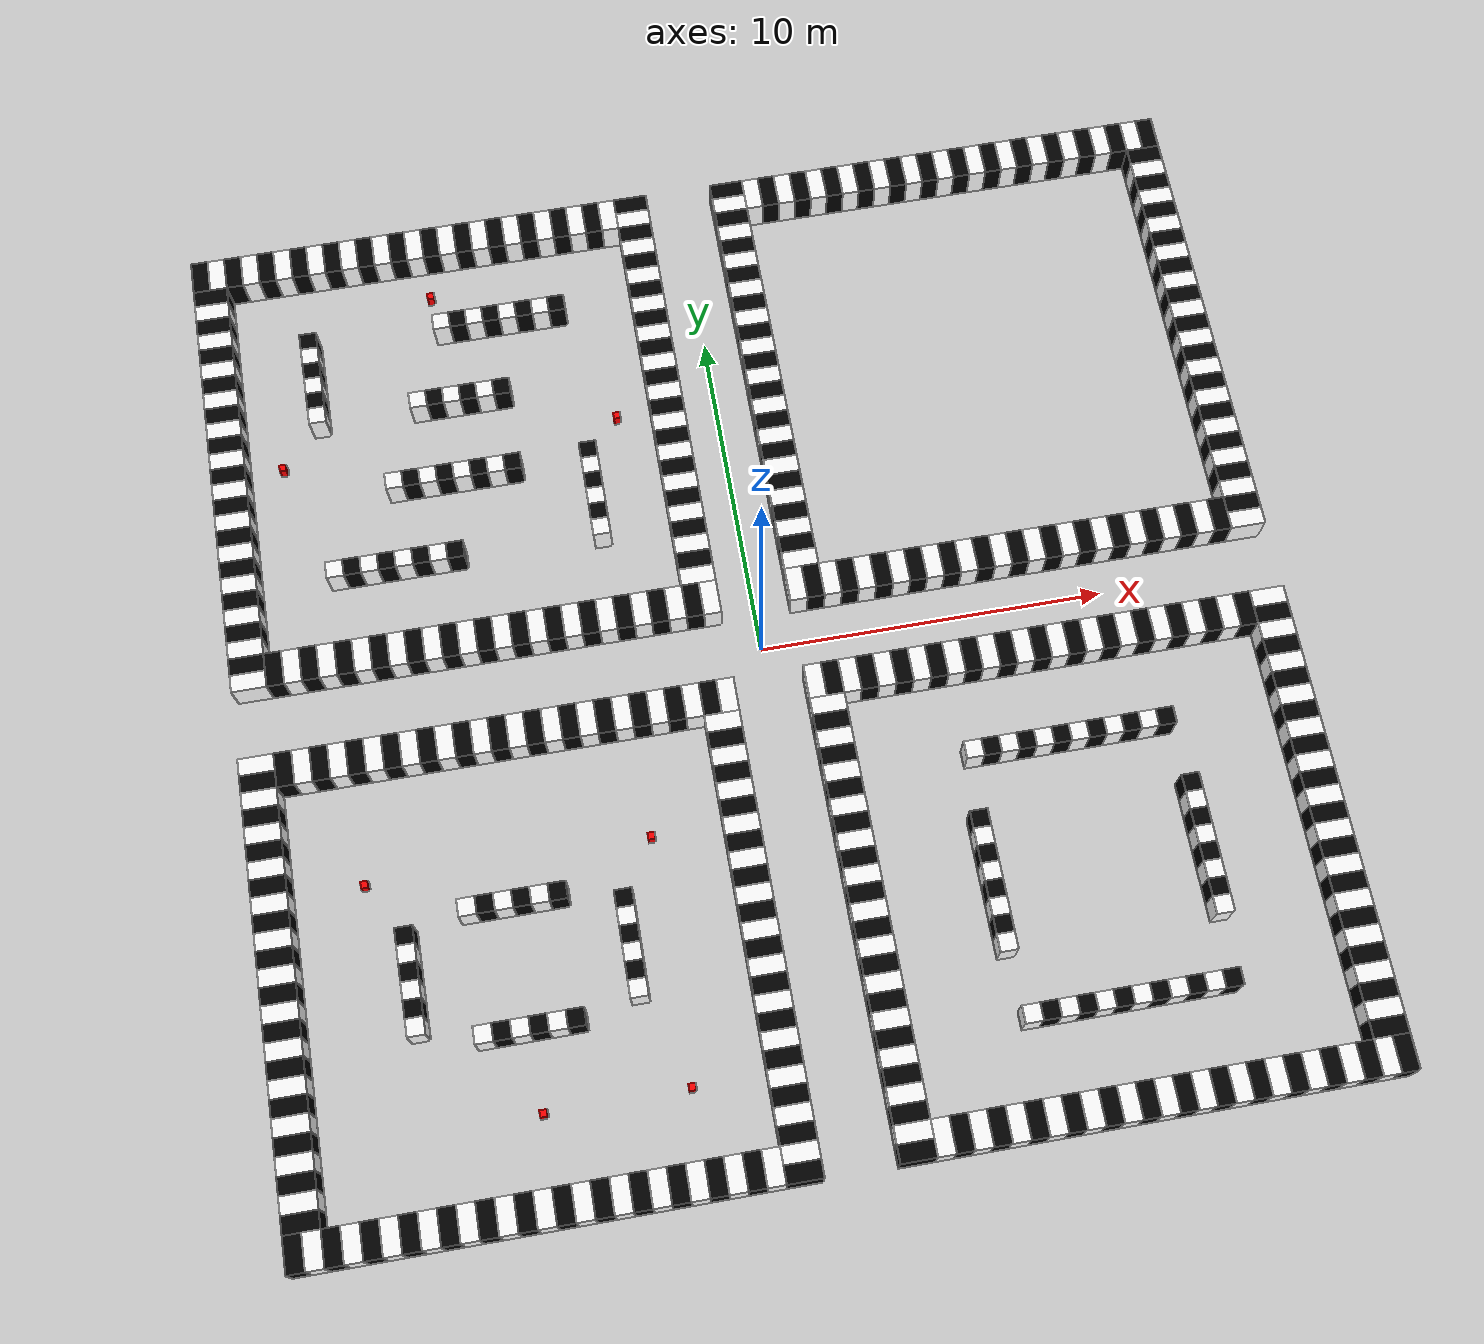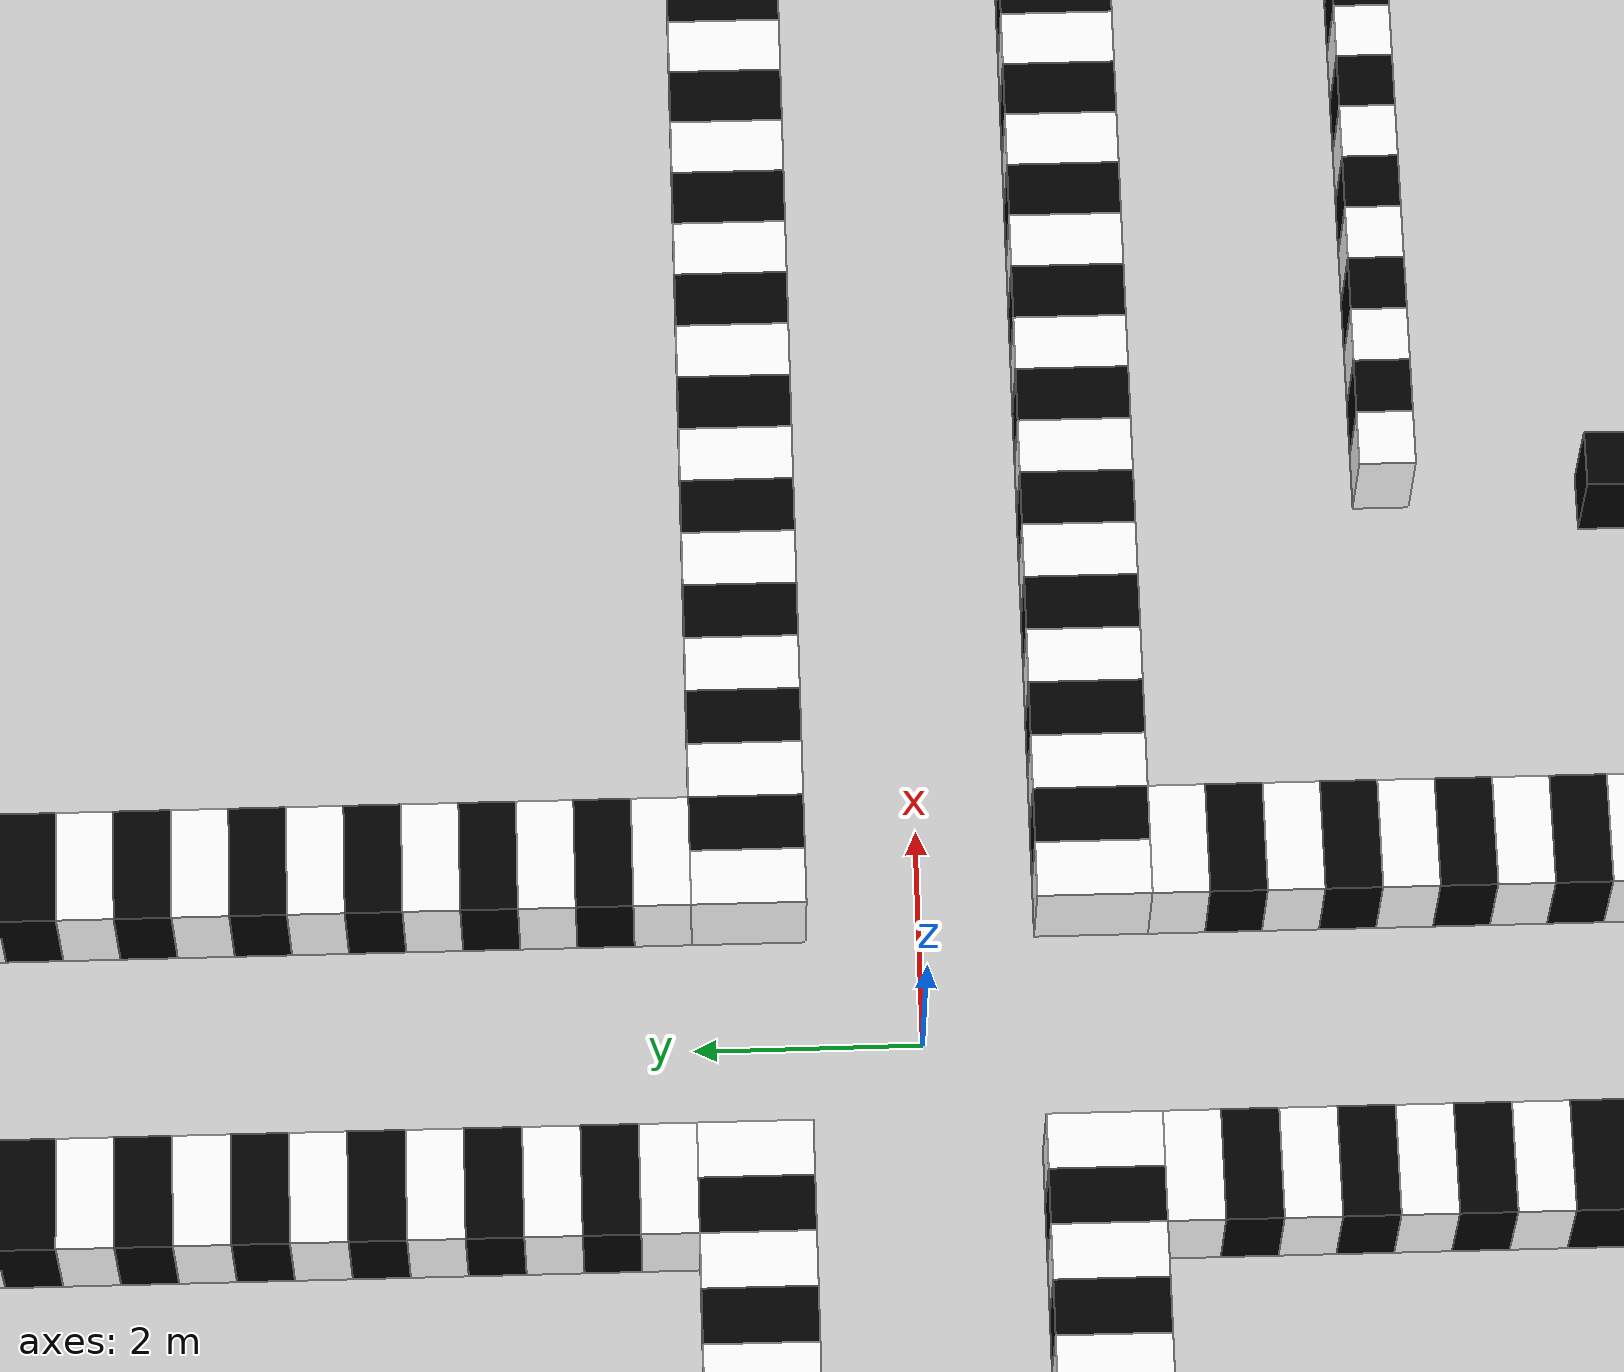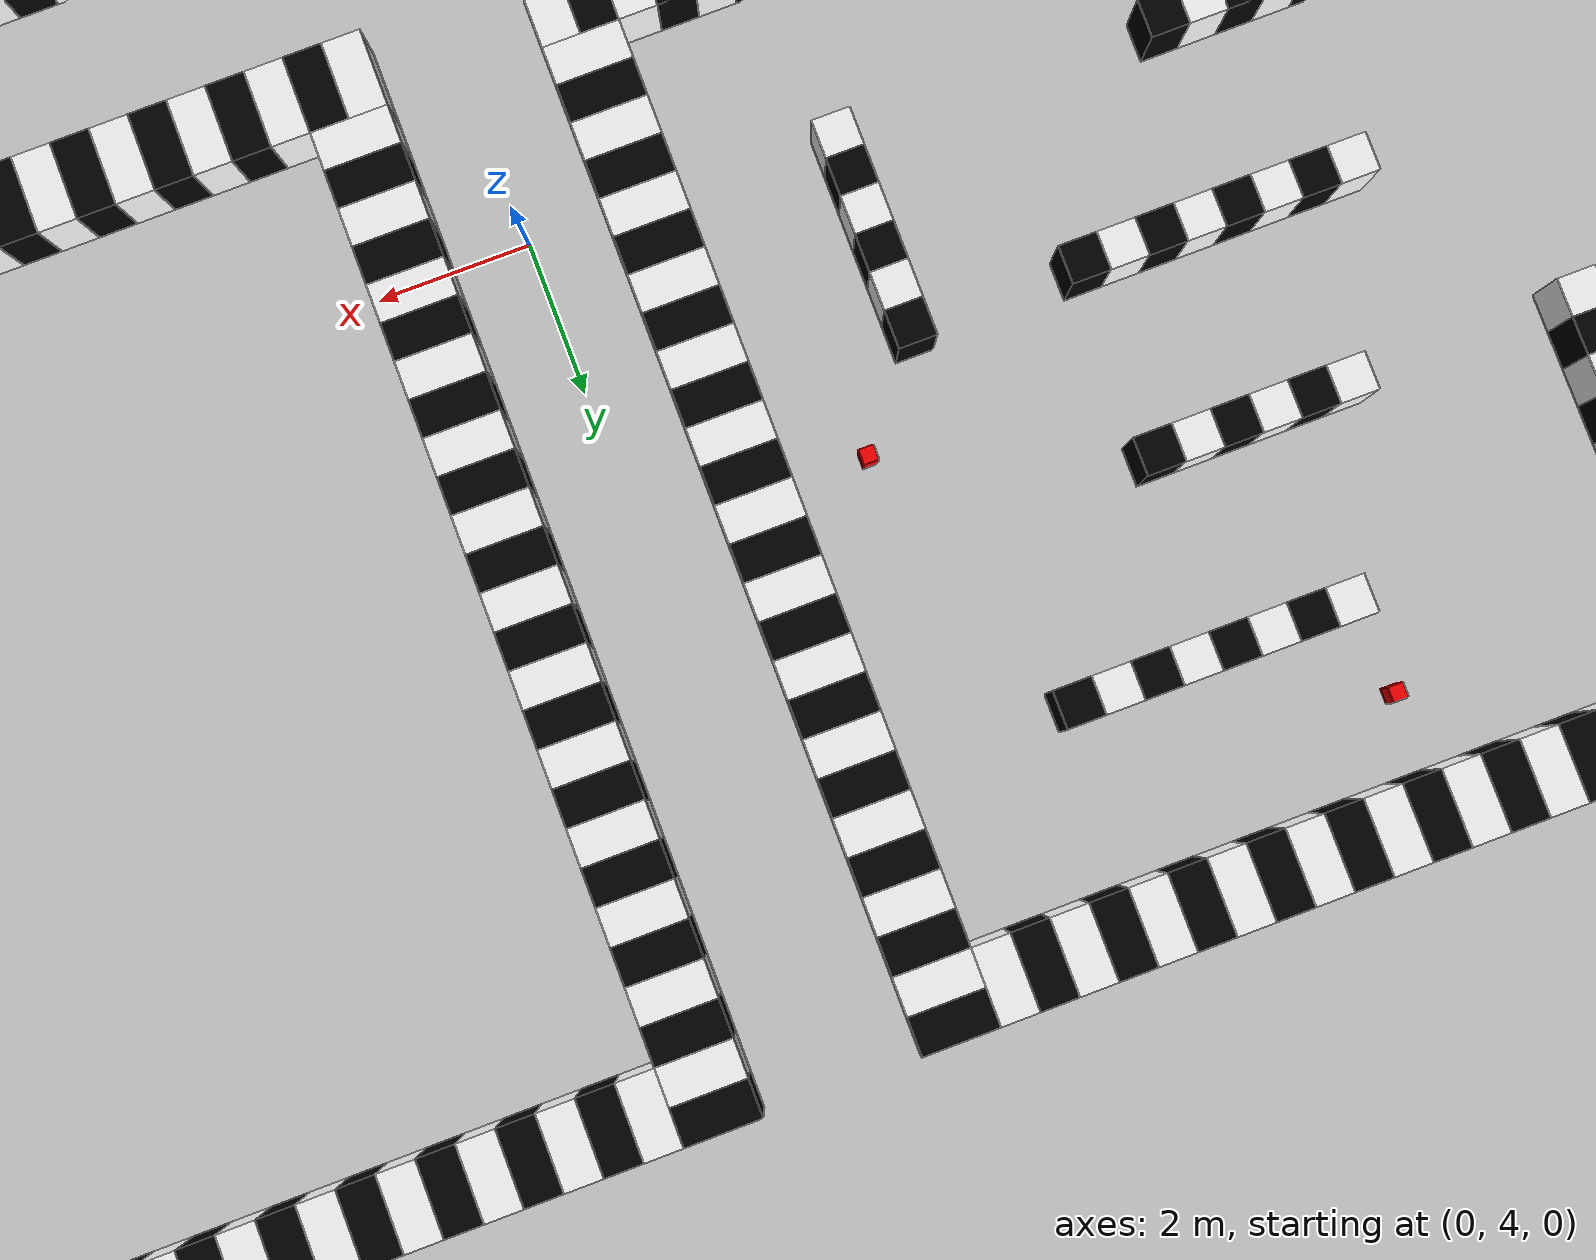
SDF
<sdf version="1.9">
 <world name="default">
  <plugin filename="gz-sim-physics-system" name="gz::sim::systems::Physics"/>
  <plugin filename="gz-sim-sensors-system" name="gz::sim::systems::Sensors">
   <render_engine>ogre2</render_engine>
  </plugin>
  <plugin filename="gz-sim-scene-broadcaster-system" name="gz::sim::systems::SceneBroadcaster"/>
  <plugin filename="gz-sim-user-commands-system" name="gz::sim::systems::UserCommands"/>
  <light name="directional_light" type="directional">
   <pose>0 0 10 0 0 0</pose>
   <diffuse>1 1 1 1</diffuse>
   <specular>0.1 0.1 0.1 1</specular>
   <direction>-0.5 0.1 -0.9</direction>
   <attenuation>
    <range>1000</range>
    <constant>0.9</constant>
    <linear>0.01</linear>
    <quadratic>0.001</quadratic>
   </attenuation>
  </light>
  <model name="ground_plane">
   <static>true</static>
   <link name="link">
    <collision name="collision">
     <geometry><plane><normal>0 0 1</normal><size>100 100</size></plane></geometry>
    </collision>
    <visual name="visual">
     <geometry><plane><normal>0 0 1</normal><size>100 100</size></plane></geometry>
     <material>
      <ambient>0.8 0.8 0.8 1</ambient>
      <diffuse>0.8 0.8 0.8 1</diffuse>
      <specular>0.8 0.8 0.8 1</specular>
     </material>
    </visual>
   </link>
  </model>
  <gravity>0 0 -9.8</gravity>
  <physics type="ode">
   <max_step_size>0.01</max_step_size>
   <real_time_factor>1</real_time_factor>
   <real_time_update_rate>100</real_time_update_rate>
  </physics>
  <model name="env1wall1">
   <static>true</static>
   <link name="link">
    <collision name="collision1">
     <geometry>
      <polyline>
       <point>-2 -2</point>
       <point>-1 -2</point>
       <point>-1 -15</point>
       <point>-2 -15</point>
       <height>1</height>
      </polyline>
     </geometry>
    </collision>
    <visual name="s1">
     <pose>-1.5 -2.25 0.5 0 0 0</pose>
     <geometry><box><size>1 0.5 1</size></box></geometry>
     <material><ambient>1 1 1 1</ambient><diffuse>1 1 1 1</diffuse></material>
    </visual>
    <visual name="s2">
     <pose>-1.5 -2.75 0.5 0 0 0</pose>
     <geometry><box><size>1 0.5 1</size></box></geometry>
     <material><ambient>0 0 0 1</ambient><diffuse>0 0 0 1</diffuse></material>
    </visual>
    <visual name="s3">
     <pose>-1.5 -3.25 0.5 0 0 0</pose>
     <geometry><box><size>1 0.5 1</size></box></geometry>
     <material><ambient>1 1 1 1</ambient><diffuse>1 1 1 1</diffuse></material>
    </visual>
    <visual name="s4">
     <pose>-1.5 -3.75 0.5 0 0 0</pose>
     <geometry><box><size>1 0.5 1</size></box></geometry>
     <material><ambient>0 0 0 1</ambient><diffuse>0 0 0 1</diffuse></material>
    </visual>
    <visual name="s5">
     <pose>-1.5 -4.25 0.5 0 0 0</pose>
     <geometry><box><size>1 0.5 1</size></box></geometry>
     <material><ambient>1 1 1 1</ambient><diffuse>1 1 1 1</diffuse></material>
    </visual>
    <visual name="s6">
     <pose>-1.5 -4.75 0.5 0 0 0</pose>
     <geometry><box><size>1 0.5 1</size></box></geometry>
     <material><ambient>0 0 0 1</ambient><diffuse>0 0 0 1</diffuse></material>
    </visual>
    <visual name="s7">
     <pose>-1.5 -5.25 0.5 0 0 0</pose>
     <geometry><box><size>1 0.5 1</size></box></geometry>
     <material><ambient>1 1 1 1</ambient><diffuse>1 1 1 1</diffuse></material>
    </visual>
    <visual name="s8">
     <pose>-1.5 -5.75 0.5 0 0 0</pose>
     <geometry><box><size>1 0.5 1</size></box></geometry>
     <material><ambient>0 0 0 1</ambient><diffuse>0 0 0 1</diffuse></material>
    </visual>
    <visual name="s9">
     <pose>-1.5 -6.25 0.5 0 0 0</pose>
     <geometry><box><size>1 0.5 1</size></box></geometry>
     <material><ambient>1 1 1 1</ambient><diffuse>1 1 1 1</diffuse></material>
    </visual>
    <visual name="s10">
     <pose>-1.5 -6.75 0.5 0 0 0</pose>
     <geometry><box><size>1 0.5 1</size></box></geometry>
     <material><ambient>0 0 0 1</ambient><diffuse>0 0 0 1</diffuse></material>
    </visual>
    <visual name="s11">
     <pose>-1.5 -7.25 0.5 0 0 0</pose>
     <geometry><box><size>1 0.5 1</size></box></geometry>
     <material><ambient>1 1 1 1</ambient><diffuse>1 1 1 1</diffuse></material>
    </visual>
    <visual name="s12">
     <pose>-1.5 -7.75 0.5 0 0 0</pose>
     <geometry><box><size>1 0.5 1</size></box></geometry>
     <material><ambient>0 0 0 1</ambient><diffuse>0 0 0 1</diffuse></material>
    </visual>
    <visual name="s13">
     <pose>-1.5 -8.25 0.5 0 0 0</pose>
     <geometry><box><size>1 0.5 1</size></box></geometry>
     <material><ambient>1 1 1 1</ambient><diffuse>1 1 1 1</diffuse></material>
    </visual>
    <visual name="s14">
     <pose>-1.5 -8.75 0.5 0 0 0</pose>
     <geometry><box><size>1 0.5 1</size></box></geometry>
     <material><ambient>0 0 0 1</ambient><diffuse>0 0 0 1</diffuse></material>
    </visual>
    <visual name="s15">
     <pose>-1.5 -9.25 0.5 0 0 0</pose>
     <geometry><box><size>1 0.5 1</size></box></geometry>
     <material><ambient>1 1 1 1</ambient><diffuse>1 1 1 1</diffuse></material>
    </visual>
    <visual name="s16">
     <pose>-1.5 -9.75 0.5 0 0 0</pose>
     <geometry><box><size>1 0.5 1</size></box></geometry>
     <material><ambient>0 0 0 1</ambient><diffuse>0 0 0 1</diffuse></material>
    </visual>
    <visual name="s17">
     <pose>-1.5 -10.25 0.5 0 0 0</pose>
     <geometry><box><size>1 0.5 1</size></box></geometry>
     <material><ambient>1 1 1 1</ambient><diffuse>1 1 1 1</diffuse></material>
    </visual>
    <visual name="s18">
     <pose>-1.5 -10.75 0.5 0 0 0</pose>
     <geometry><box><size>1 0.5 1</size></box></geometry>
     <material><ambient>0 0 0 1</ambient><diffuse>0 0 0 1</diffuse></material>
    </visual>
    <visual name="s19">
     <pose>-1.5 -11.25 0.5 0 0 0</pose>
     <geometry><box><size>1 0.5 1</size></box></geometry>
     <material><ambient>1 1 1 1</ambient><diffuse>1 1 1 1</diffuse></material>
    </visual>
    <visual name="s20">
     <pose>-1.5 -11.75 0.5 0 0 0</pose>
     <geometry><box><size>1 0.5 1</size></box></geometry>
     <material><ambient>0 0 0 1</ambient><diffuse>0 0 0 1</diffuse></material>
    </visual>
    <visual name="s21">
     <pose>-1.5 -12.25 0.5 0 0 0</pose>
     <geometry><box><size>1 0.5 1</size></box></geometry>
     <material><ambient>1 1 1 1</ambient><diffuse>1 1 1 1</diffuse></material>
    </visual>
    <visual name="s22">
     <pose>-1.5 -12.75 0.5 0 0 0</pose>
     <geometry><box><size>1 0.5 1</size></box></geometry>
     <material><ambient>0 0 0 1</ambient><diffuse>0 0 0 1</diffuse></material>
    </visual>
    <visual name="s23">
     <pose>-1.5 -13.25 0.5 0 0 0</pose>
     <geometry><box><size>1 0.5 1</size></box></geometry>
     <material><ambient>1 1 1 1</ambient><diffuse>1 1 1 1</diffuse></material>
    </visual>
    <visual name="s24">
     <pose>-1.5 -13.75 0.5 0 0 0</pose>
     <geometry><box><size>1 0.5 1</size></box></geometry>
     <material><ambient>0 0 0 1</ambient><diffuse>0 0 0 1</diffuse></material>
    </visual>
    <visual name="s25">
     <pose>-1.5 -14.25 0.5 0 0 0</pose>
     <geometry><box><size>1 0.5 1</size></box></geometry>
     <material><ambient>1 1 1 1</ambient><diffuse>1 1 1 1</diffuse></material>
    </visual>
    <visual name="s26">
     <pose>-1.5 -14.75 0.5 0 0 0</pose>
     <geometry><box><size>1 0.5 1</size></box></geometry>
     <material><ambient>0 0 0 1</ambient><diffuse>0 0 0 1</diffuse></material>
    </visual>
   </link>
  </model>
  <model name="env1wall2">
   <static>true</static>
   <link name="link">
    <collision name="collision1">
     <geometry>
      <polyline>
       <point>-2 -14</point>
       <point>-2 -15</point>
       <point>-15 -15</point>
       <point>-15 -14</point>
       <height>1</height>
      </polyline>
     </geometry>
    </collision>
    <visual name="s1">
     <pose>-2.25 -14.5 0.5 0 0 0</pose>
     <geometry><box><size>0.5 1 1</size></box></geometry>
     <material><ambient>1 1 1 1</ambient><diffuse>1 1 1 1</diffuse></material>
    </visual>
    <visual name="s2">
     <pose>-2.75 -14.5 0.5 0 0 0</pose>
     <geometry><box><size>0.5 1 1</size></box></geometry>
     <material><ambient>0 0 0 1</ambient><diffuse>0 0 0 1</diffuse></material>
    </visual>
    <visual name="s3">
     <pose>-3.25 -14.5 0.5 0 0 0</pose>
     <geometry><box><size>0.5 1 1</size></box></geometry>
     <material><ambient>1 1 1 1</ambient><diffuse>1 1 1 1</diffuse></material>
    </visual>
    <visual name="s4">
     <pose>-3.75 -14.5 0.5 0 0 0</pose>
     <geometry><box><size>0.5 1 1</size></box></geometry>
     <material><ambient>0 0 0 1</ambient><diffuse>0 0 0 1</diffuse></material>
    </visual>
    <visual name="s5">
     <pose>-4.25 -14.5 0.5 0 0 0</pose>
     <geometry><box><size>0.5 1 1</size></box></geometry>
     <material><ambient>1 1 1 1</ambient><diffuse>1 1 1 1</diffuse></material>
    </visual>
    <visual name="s6">
     <pose>-4.75 -14.5 0.5 0 0 0</pose>
     <geometry><box><size>0.5 1 1</size></box></geometry>
     <material><ambient>0 0 0 1</ambient><diffuse>0 0 0 1</diffuse></material>
    </visual>
    <visual name="s7">
     <pose>-5.25 -14.5 0.5 0 0 0</pose>
     <geometry><box><size>0.5 1 1</size></box></geometry>
     <material><ambient>1 1 1 1</ambient><diffuse>1 1 1 1</diffuse></material>
    </visual>
    <visual name="s8">
     <pose>-5.75 -14.5 0.5 0 0 0</pose>
     <geometry><box><size>0.5 1 1</size></box></geometry>
     <material><ambient>0 0 0 1</ambient><diffuse>0 0 0 1</diffuse></material>
    </visual>
    <visual name="s9">
     <pose>-6.25 -14.5 0.5 0 0 0</pose>
     <geometry><box><size>0.5 1 1</size></box></geometry>
     <material><ambient>1 1 1 1</ambient><diffuse>1 1 1 1</diffuse></material>
    </visual>
    <visual name="s10">
     <pose>-6.75 -14.5 0.5 0 0 0</pose>
     <geometry><box><size>0.5 1 1</size></box></geometry>
     <material><ambient>0 0 0 1</ambient><diffuse>0 0 0 1</diffuse></material>
    </visual>
    <visual name="s11">
     <pose>-7.25 -14.5 0.5 0 0 0</pose>
     <geometry><box><size>0.5 1 1</size></box></geometry>
     <material><ambient>1 1 1 1</ambient><diffuse>1 1 1 1</diffuse></material>
    </visual>
    <visual name="s12">
     <pose>-7.75 -14.5 0.5 0 0 0</pose>
     <geometry><box><size>0.5 1 1</size></box></geometry>
     <material><ambient>0 0 0 1</ambient><diffuse>0 0 0 1</diffuse></material>
    </visual>
    <visual name="s13">
     <pose>-8.25 -14.5 0.5 0 0 0</pose>
     <geometry><box><size>0.5 1 1</size></box></geometry>
     <material><ambient>1 1 1 1</ambient><diffuse>1 1 1 1</diffuse></material>
    </visual>
    <visual name="s14">
     <pose>-8.75 -14.5 0.5 0 0 0</pose>
     <geometry><box><size>0.5 1 1</size></box></geometry>
     <material><ambient>0 0 0 1</ambient><diffuse>0 0 0 1</diffuse></material>
    </visual>
    <visual name="s15">
     <pose>-9.25 -14.5 0.5 0 0 0</pose>
     <geometry><box><size>0.5 1 1</size></box></geometry>
     <material><ambient>1 1 1 1</ambient><diffuse>1 1 1 1</diffuse></material>
    </visual>
    <visual name="s16">
     <pose>-9.75 -14.5 0.5 0 0 0</pose>
     <geometry><box><size>0.5 1 1</size></box></geometry>
     <material><ambient>0 0 0 1</ambient><diffuse>0 0 0 1</diffuse></material>
    </visual>
    <visual name="s17">
     <pose>-10.25 -14.5 0.5 0 0 0</pose>
     <geometry><box><size>0.5 1 1</size></box></geometry>
     <material><ambient>1 1 1 1</ambient><diffuse>1 1 1 1</diffuse></material>
    </visual>
    <visual name="s18">
     <pose>-10.75 -14.5 0.5 0 0 0</pose>
     <geometry><box><size>0.5 1 1</size></box></geometry>
     <material><ambient>0 0 0 1</ambient><diffuse>0 0 0 1</diffuse></material>
    </visual>
    <visual name="s19">
     <pose>-11.25 -14.5 0.5 0 0 0</pose>
     <geometry><box><size>0.5 1 1</size></box></geometry>
     <material><ambient>1 1 1 1</ambient><diffuse>1 1 1 1</diffuse></material>
    </visual>
    <visual name="s20">
     <pose>-11.75 -14.5 0.5 0 0 0</pose>
     <geometry><box><size>0.5 1 1</size></box></geometry>
     <material><ambient>0 0 0 1</ambient><diffuse>0 0 0 1</diffuse></material>
    </visual>
    <visual name="s21">
     <pose>-12.25 -14.5 0.5 0 0 0</pose>
     <geometry><box><size>0.5 1 1</size></box></geometry>
     <material><ambient>1 1 1 1</ambient><diffuse>1 1 1 1</diffuse></material>
    </visual>
    <visual name="s22">
     <pose>-12.75 -14.5 0.5 0 0 0</pose>
     <geometry><box><size>0.5 1 1</size></box></geometry>
     <material><ambient>0 0 0 1</ambient><diffuse>0 0 0 1</diffuse></material>
    </visual>
    <visual name="s23">
     <pose>-13.25 -14.5 0.5 0 0 0</pose>
     <geometry><box><size>0.5 1 1</size></box></geometry>
     <material><ambient>1 1 1 1</ambient><diffuse>1 1 1 1</diffuse></material>
    </visual>
    <visual name="s24">
     <pose>-13.75 -14.5 0.5 0 0 0</pose>
     <geometry><box><size>0.5 1 1</size></box></geometry>
     <material><ambient>0 0 0 1</ambient><diffuse>0 0 0 1</diffuse></material>
    </visual>
    <visual name="s25">
     <pose>-14.25 -14.5 0.5 0 0 0</pose>
     <geometry><box><size>0.5 1 1</size></box></geometry>
     <material><ambient>1 1 1 1</ambient><diffuse>1 1 1 1</diffuse></material>
    </visual>
    <visual name="s26">
     <pose>-14.75 -14.5 0.5 0 0 0</pose>
     <geometry><box><size>0.5 1 1</size></box></geometry>
     <material><ambient>0 0 0 1</ambient><diffuse>0 0 0 1</diffuse></material>
    </visual>
   </link>
  </model>
  <model name="env1wall3">
   <static>true</static>
   <link name="link">
    <collision name="collision1">
     <geometry>
      <polyline>
       <point>-14 -1</point>
       <point>-14 -14</point>
       <point>-15 -14</point>
       <point>-15 -1</point>
       <height>1</height>
      </polyline>
     </geometry>
    </collision>
    <visual name="s1">
     <pose>-14.5 -1.25 0.5 0 0 0</pose>
     <geometry><box><size>1 0.5 1</size></box></geometry>
     <material><ambient>1 1 1 1</ambient><diffuse>1 1 1 1</diffuse></material>
    </visual>
    <visual name="s2">
     <pose>-14.5 -1.75 0.5 0 0 0</pose>
     <geometry><box><size>1 0.5 1</size></box></geometry>
     <material><ambient>0 0 0 1</ambient><diffuse>0 0 0 1</diffuse></material>
    </visual>
    <visual name="s3">
     <pose>-14.5 -2.25 0.5 0 0 0</pose>
     <geometry><box><size>1 0.5 1</size></box></geometry>
     <material><ambient>1 1 1 1</ambient><diffuse>1 1 1 1</diffuse></material>
    </visual>
    <visual name="s4">
     <pose>-14.5 -2.75 0.5 0 0 0</pose>
     <geometry><box><size>1 0.5 1</size></box></geometry>
     <material><ambient>0 0 0 1</ambient><diffuse>0 0 0 1</diffuse></material>
    </visual>
    <visual name="s5">
     <pose>-14.5 -3.25 0.5 0 0 0</pose>
     <geometry><box><size>1 0.5 1</size></box></geometry>
     <material><ambient>1 1 1 1</ambient><diffuse>1 1 1 1</diffuse></material>
    </visual>
    <visual name="s6">
     <pose>-14.5 -3.75 0.5 0 0 0</pose>
     <geometry><box><size>1 0.5 1</size></box></geometry>
     <material><ambient>0 0 0 1</ambient><diffuse>0 0 0 1</diffuse></material>
    </visual>
    <visual name="s7">
     <pose>-14.5 -4.25 0.5 0 0 0</pose>
     <geometry><box><size>1 0.5 1</size></box></geometry>
     <material><ambient>1 1 1 1</ambient><diffuse>1 1 1 1</diffuse></material>
    </visual>
    <visual name="s8">
     <pose>-14.5 -4.75 0.5 0 0 0</pose>
     <geometry><box><size>1 0.5 1</size></box></geometry>
     <material><ambient>0 0 0 1</ambient><diffuse>0 0 0 1</diffuse></material>
    </visual>
    <visual name="s9">
     <pose>-14.5 -5.25 0.5 0 0 0</pose>
     <geometry><box><size>1 0.5 1</size></box></geometry>
     <material><ambient>1 1 1 1</ambient><diffuse>1 1 1 1</diffuse></material>
    </visual>
    <visual name="s10">
     <pose>-14.5 -5.75 0.5 0 0 0</pose>
     <geometry><box><size>1 0.5 1</size></box></geometry>
     <material><ambient>0 0 0 1</ambient><diffuse>0 0 0 1</diffuse></material>
    </visual>
    <visual name="s11">
     <pose>-14.5 -6.25 0.5 0 0 0</pose>
     <geometry><box><size>1 0.5 1</size></box></geometry>
     <material><ambient>1 1 1 1</ambient><diffuse>1 1 1 1</diffuse></material>
    </visual>
    <visual name="s12">
     <pose>-14.5 -6.75 0.5 0 0 0</pose>
     <geometry><box><size>1 0.5 1</size></box></geometry>
     <material><ambient>0 0 0 1</ambient><diffuse>0 0 0 1</diffuse></material>
    </visual>
    <visual name="s13">
     <pose>-14.5 -7.25 0.5 0 0 0</pose>
     <geometry><box><size>1 0.5 1</size></box></geometry>
     <material><ambient>1 1 1 1</ambient><diffuse>1 1 1 1</diffuse></material>
    </visual>
    <visual name="s14">
     <pose>-14.5 -7.75 0.5 0 0 0</pose>
     <geometry><box><size>1 0.5 1</size></box></geometry>
     <material><ambient>0 0 0 1</ambient><diffuse>0 0 0 1</diffuse></material>
    </visual>
    <visual name="s15">
     <pose>-14.5 -8.25 0.5 0 0 0</pose>
     <geometry><box><size>1 0.5 1</size></box></geometry>
     <material><ambient>1 1 1 1</ambient><diffuse>1 1 1 1</diffuse></material>
    </visual>
    <visual name="s16">
     <pose>-14.5 -8.75 0.5 0 0 0</pose>
     <geometry><box><size>1 0.5 1</size></box></geometry>
     <material><ambient>0 0 0 1</ambient><diffuse>0 0 0 1</diffuse></material>
    </visual>
    <visual name="s17">
     <pose>-14.5 -9.25 0.5 0 0 0</pose>
     <geometry><box><size>1 0.5 1</size></box></geometry>
     <material><ambient>1 1 1 1</ambient><diffuse>1 1 1 1</diffuse></material>
    </visual>
    <visual name="s18">
     <pose>-14.5 -9.75 0.5 0 0 0</pose>
     <geometry><box><size>1 0.5 1</size></box></geometry>
     <material><ambient>0 0 0 1</ambient><diffuse>0 0 0 1</diffuse></material>
    </visual>
    <visual name="s19">
     <pose>-14.5 -10.25 0.5 0 0 0</pose>
     <geometry><box><size>1 0.5 1</size></box></geometry>
     <material><ambient>1 1 1 1</ambient><diffuse>1 1 1 1</diffuse></material>
    </visual>
    <visual name="s20">
     <pose>-14.5 -10.75 0.5 0 0 0</pose>
     <geometry><box><size>1 0.5 1</size></box></geometry>
     <material><ambient>0 0 0 1</ambient><diffuse>0 0 0 1</diffuse></material>
    </visual>
    <visual name="s21">
     <pose>-14.5 -11.25 0.5 0 0 0</pose>
     <geometry><box><size>1 0.5 1</size></box></geometry>
     <material><ambient>1 1 1 1</ambient><diffuse>1 1 1 1</diffuse></material>
    </visual>
    <visual name="s22">
     <pose>-14.5 -11.75 0.5 0 0 0</pose>
     <geometry><box><size>1 0.5 1</size></box></geometry>
     <material><ambient>0 0 0 1</ambient><diffuse>0 0 0 1</diffuse></material>
    </visual>
    <visual name="s23">
     <pose>-14.5 -12.25 0.5 0 0 0</pose>
     <geometry><box><size>1 0.5 1</size></box></geometry>
     <material><ambient>1 1 1 1</ambient><diffuse>1 1 1 1</diffuse></material>
    </visual>
    <visual name="s24">
     <pose>-14.5 -12.75 0.5 0 0 0</pose>
     <geometry><box><size>1 0.5 1</size></box></geometry>
     <material><ambient>0 0 0 1</ambient><diffuse>0 0 0 1</diffuse></material>
    </visual>
    <visual name="s25">
     <pose>-14.5 -13.25 0.5 0 0 0</pose>
     <geometry><box><size>1 0.5 1</size></box></geometry>
     <material><ambient>1 1 1 1</ambient><diffuse>1 1 1 1</diffuse></material>
    </visual>
    <visual name="s26">
     <pose>-14.5 -13.75 0.5 0 0 0</pose>
     <geometry><box><size>1 0.5 1</size></box></geometry>
     <material><ambient>0 0 0 1</ambient><diffuse>0 0 0 1</diffuse></material>
    </visual>
   </link>
  </model>
  <model name="env1wall4">
   <static>true</static>
   <link name="link">
    <collision name="collision1">
     <geometry>
      <polyline>
       <point>-1 -1</point>
       <point>-1 -2</point>
       <point>-14 -2</point>
       <point>-14 -1</point>
       <height>1</height>
      </polyline>
     </geometry>
    </collision>
    <visual name="s1">
     <pose>-1.25 -1.5 0.5 0 0 0</pose>
     <geometry><box><size>0.5 1 1</size></box></geometry>
     <material><ambient>1 1 1 1</ambient><diffuse>1 1 1 1</diffuse></material>
    </visual>
    <visual name="s2">
     <pose>-1.75 -1.5 0.5 0 0 0</pose>
     <geometry><box><size>0.5 1 1</size></box></geometry>
     <material><ambient>0 0 0 1</ambient><diffuse>0 0 0 1</diffuse></material>
    </visual>
    <visual name="s3">
     <pose>-2.25 -1.5 0.5 0 0 0</pose>
     <geometry><box><size>0.5 1 1</size></box></geometry>
     <material><ambient>1 1 1 1</ambient><diffuse>1 1 1 1</diffuse></material>
    </visual>
    <visual name="s4">
     <pose>-2.75 -1.5 0.5 0 0 0</pose>
     <geometry><box><size>0.5 1 1</size></box></geometry>
     <material><ambient>0 0 0 1</ambient><diffuse>0 0 0 1</diffuse></material>
    </visual>
    <visual name="s5">
     <pose>-3.25 -1.5 0.5 0 0 0</pose>
     <geometry><box><size>0.5 1 1</size></box></geometry>
     <material><ambient>1 1 1 1</ambient><diffuse>1 1 1 1</diffuse></material>
    </visual>
    <visual name="s6">
     <pose>-3.75 -1.5 0.5 0 0 0</pose>
     <geometry><box><size>0.5 1 1</size></box></geometry>
     <material><ambient>0 0 0 1</ambient><diffuse>0 0 0 1</diffuse></material>
    </visual>
    <visual name="s7">
     <pose>-4.25 -1.5 0.5 0 0 0</pose>
     <geometry><box><size>0.5 1 1</size></box></geometry>
     <material><ambient>1 1 1 1</ambient><diffuse>1 1 1 1</diffuse></material>
    </visual>
    <visual name="s8">
     <pose>-4.75 -1.5 0.5 0 0 0</pose>
     <geometry><box><size>0.5 1 1</size></box></geometry>
     <material><ambient>0 0 0 1</ambient><diffuse>0 0 0 1</diffuse></material>
    </visual>
    <visual name="s9">
     <pose>-5.25 -1.5 0.5 0 0 0</pose>
     <geometry><box><size>0.5 1 1</size></box></geometry>
     <material><ambient>1 1 1 1</ambient><diffuse>1 1 1 1</diffuse></material>
    </visual>
    <visual name="s10">
     <pose>-5.75 -1.5 0.5 0 0 0</pose>
     <geometry><box><size>0.5 1 1</size></box></geometry>
     <material><ambient>0 0 0 1</ambient><diffuse>0 0 0 1</diffuse></material>
    </visual>
    <visual name="s11">
     <pose>-6.25 -1.5 0.5 0 0 0</pose>
     <geometry><box><size>0.5 1 1</size></box></geometry>
     <material><ambient>1 1 1 1</ambient><diffuse>1 1 1 1</diffuse></material>
    </visual>
    <visual name="s12">
     <pose>-6.75 -1.5 0.5 0 0 0</pose>
     <geometry><box><size>0.5 1 1</size></box></geometry>
     <material><ambient>0 0 0 1</ambient><diffuse>0 0 0 1</diffuse></material>
    </visual>
    <visual name="s13">
     <pose>-7.25 -1.5 0.5 0 0 0</pose>
     <geometry><box><size>0.5 1 1</size></box></geometry>
     <material><ambient>1 1 1 1</ambient><diffuse>1 1 1 1</diffuse></material>
    </visual>
    <visual name="s14">
     <pose>-7.75 -1.5 0.5 0 0 0</pose>
     <geometry><box><size>0.5 1 1</size></box></geometry>
     <material><ambient>0 0 0 1</ambient><diffuse>0 0 0 1</diffuse></material>
    </visual>
    <visual name="s15">
     <pose>-8.25 -1.5 0.5 0 0 0</pose>
     <geometry><box><size>0.5 1 1</size></box></geometry>
     <material><ambient>1 1 1 1</ambient><diffuse>1 1 1 1</diffuse></material>
    </visual>
    <visual name="s16">
     <pose>-8.75 -1.5 0.5 0 0 0</pose>
     <geometry><box><size>0.5 1 1</size></box></geometry>
     <material><ambient>0 0 0 1</ambient><diffuse>0 0 0 1</diffuse></material>
    </visual>
    <visual name="s17">
     <pose>-9.25 -1.5 0.5 0 0 0</pose>
     <geometry><box><size>0.5 1 1</size></box></geometry>
     <material><ambient>1 1 1 1</ambient><diffuse>1 1 1 1</diffuse></material>
    </visual>
    <visual name="s18">
     <pose>-9.75 -1.5 0.5 0 0 0</pose>
     <geometry><box><size>0.5 1 1</size></box></geometry>
     <material><ambient>0 0 0 1</ambient><diffuse>0 0 0 1</diffuse></material>
    </visual>
    <visual name="s19">
     <pose>-10.25 -1.5 0.5 0 0 0</pose>
     <geometry><box><size>0.5 1 1</size></box></geometry>
     <material><ambient>1 1 1 1</ambient><diffuse>1 1 1 1</diffuse></material>
    </visual>
    <visual name="s20">
     <pose>-10.75 -1.5 0.5 0 0 0</pose>
     <geometry><box><size>0.5 1 1</size></box></geometry>
     <material><ambient>0 0 0 1</ambient><diffuse>0 0 0 1</diffuse></material>
    </visual>
    <visual name="s21">
     <pose>-11.25 -1.5 0.5 0 0 0</pose>
     <geometry><box><size>0.5 1 1</size></box></geometry>
     <material><ambient>1 1 1 1</ambient><diffuse>1 1 1 1</diffuse></material>
    </visual>
    <visual name="s22">
     <pose>-11.75 -1.5 0.5 0 0 0</pose>
     <geometry><box><size>0.5 1 1</size></box></geometry>
     <material><ambient>0 0 0 1</ambient><diffuse>0 0 0 1</diffuse></material>
    </visual>
    <visual name="s23">
     <pose>-12.25 -1.5 0.5 0 0 0</pose>
     <geometry><box><size>0.5 1 1</size></box></geometry>
     <material><ambient>1 1 1 1</ambient><diffuse>1 1 1 1</diffuse></material>
    </visual>
    <visual name="s24">
     <pose>-12.75 -1.5 0.5 0 0 0</pose>
     <geometry><box><size>0.5 1 1</size></box></geometry>
     <material><ambient>0 0 0 1</ambient><diffuse>0 0 0 1</diffuse></material>
    </visual>
    <visual name="s25">
     <pose>-13.25 -1.5 0.5 0 0 0</pose>
     <geometry><box><size>0.5 1 1</size></box></geometry>
     <material><ambient>1 1 1 1</ambient><diffuse>1 1 1 1</diffuse></material>
    </visual>
    <visual name="s26">
     <pose>-13.75 -1.5 0.5 0 0 0</pose>
     <geometry><box><size>0.5 1 1</size></box></geometry>
     <material><ambient>0 0 0 1</ambient><diffuse>0 0 0 1</diffuse></material>
    </visual>
   </link>
  </model>
  <model name="env1obs1">
   <static>true</static>
   <link name="link">
    <collision name="collision1">
     <geometry>
      <polyline>
       <point>-6.5 -6.5</point>
       <point>-6.5 -6</point>
       <point>-9.5 -6</point>
       <point>-9.5 -6.5</point>
       <height>1</height>
      </polyline>
     </geometry>
    </collision>
    <visual name="s1">
     <pose>-9.25 -6.25 0.5 0 0 0</pose>
     <geometry><box><size>0.5 0.5 1</size></box></geometry>
     <material><ambient>1 1 1 1</ambient><diffuse>1 1 1 1</diffuse></material>
    </visual>
    <visual name="s2">
     <pose>-8.75 -6.25 0.5 0 0 0</pose>
     <geometry><box><size>0.5 0.5 1</size></box></geometry>
     <material><ambient>0 0 0 1</ambient><diffuse>0 0 0 1</diffuse></material>
    </visual>
    <visual name="s3">
     <pose>-8.25 -6.25 0.5 0 0 0</pose>
     <geometry><box><size>0.5 0.5 1</size></box></geometry>
     <material><ambient>1 1 1 1</ambient><diffuse>1 1 1 1</diffuse></material>
    </visual>
    <visual name="s4">
     <pose>-7.75 -6.25 0.5 0 0 0</pose>
     <geometry><box><size>0.5 0.5 1</size></box></geometry>
     <material><ambient>0 0 0 1</ambient><diffuse>0 0 0 1</diffuse></material>
    </visual>
    <visual name="s5">
     <pose>-7.25 -6.25 0.5 0 0 0</pose>
     <geometry><box><size>0.5 0.5 1</size></box></geometry>
     <material><ambient>1 1 1 1</ambient><diffuse>1 1 1 1</diffuse></material>
    </visual>
    <visual name="s6">
     <pose>-6.75 -6.25 0.5 0 0 0</pose>
     <geometry><box><size>0.5 0.5 1</size></box></geometry>
     <material><ambient>0 0 0 1</ambient><diffuse>0 0 0 1</diffuse></material>
    </visual>
   </link>
  </model>
  <model name="env1obs2">
   <static>true</static>
   <link name="link">
    <collision name="collision1">
     <geometry>
      <polyline>
       <point>-6.5 -9.5</point>
       <point>-6.5 -10</point>
       <point>-9.5 -10</point>
       <point>-9.5 -9.5</point>
       <height>1</height>
      </polyline>
     </geometry>
    </collision>
    <visual name="s1">
     <pose>-9.25 -9.75 0.5 0 0 0</pose>
     <geometry><box><size>0.5 0.5 1</size></box></geometry>
     <material><ambient>1 1 1 1</ambient><diffuse>1 1 1 1</diffuse></material>
    </visual>
    <visual name="s2">
     <pose>-8.75 -9.75 0.5 0 0 0</pose>
     <geometry><box><size>0.5 0.5 1</size></box></geometry>
     <material><ambient>0 0 0 1</ambient><diffuse>0 0 0 1</diffuse></material>
    </visual>
    <visual name="s3">
     <pose>-8.25 -9.75 0.5 0 0 0</pose>
     <geometry><box><size>0.5 0.5 1</size></box></geometry>
     <material><ambient>1 1 1 1</ambient><diffuse>1 1 1 1</diffuse></material>
    </visual>
    <visual name="s4">
     <pose>-7.75 -9.75 0.5 0 0 0</pose>
     <geometry><box><size>0.5 0.5 1</size></box></geometry>
     <material><ambient>0 0 0 1</ambient><diffuse>0 0 0 1</diffuse></material>
    </visual>
    <visual name="s5">
     <pose>-7.25 -9.75 0.5 0 0 0</pose>
     <geometry><box><size>0.5 0.5 1</size></box></geometry>
     <material><ambient>1 1 1 1</ambient><diffuse>1 1 1 1</diffuse></material>
    </visual>
    <visual name="s6">
     <pose>-6.75 -9.75 0.5 0 0 0</pose>
     <geometry><box><size>0.5 0.5 1</size></box></geometry>
     <material><ambient>0 0 0 1</ambient><diffuse>0 0 0 1</diffuse></material>
    </visual>
   </link>
  </model>
  <model name="env1obs3">
   <static>true</static>
   <link name="link">
    <collision name="collision1">
     <geometry>
      <polyline>
       <point>-5.25 -6.5</point>
       <point>-4.75 -6.5</point>
       <point>-4.75 -9.5</point>
       <point>-5.25 -9.5</point>
       <height>1</height>
      </polyline>
     </geometry>
    </collision>
    <visual name="s1">
     <pose>-5 -9.25 0.5 0 0 0</pose>
     <geometry><box><size>0.5 0.5 1</size></box></geometry>
     <material><ambient>1 1 1 1</ambient><diffuse>1 1 1 1</diffuse></material>
    </visual>
    <visual name="s2">
     <pose>-5 -8.75 0.5 0 0 0</pose>
     <geometry><box><size>0.5 0.5 1</size></box></geometry>
     <material><ambient>0 0 0 1</ambient><diffuse>0 0 0 1</diffuse></material>
    </visual>
    <visual name="s3">
     <pose>-5 -8.25 0.5 0 0 0</pose>
     <geometry><box><size>0.5 0.5 1</size></box></geometry>
     <material><ambient>1 1 1 1</ambient><diffuse>1 1 1 1</diffuse></material>
    </visual>
    <visual name="s4">
     <pose>-5 -7.75 0.5 0 0 0</pose>
     <geometry><box><size>0.5 0.5 1</size></box></geometry>
     <material><ambient>0 0 0 1</ambient><diffuse>0 0 0 1</diffuse></material>
    </visual>
    <visual name="s5">
     <pose>-5 -7.25 0.5 0 0 0</pose>
     <geometry><box><size>0.5 0.5 1</size></box></geometry>
     <material><ambient>1 1 1 1</ambient><diffuse>1 1 1 1</diffuse></material>
    </visual>
    <visual name="s6">
     <pose>-5 -6.75 0.5 0 0 0</pose>
     <geometry><box><size>0.5 0.5 1</size></box></geometry>
     <material><ambient>0 0 0 1</ambient><diffuse>0 0 0 1</diffuse></material>
    </visual>
   </link>
  </model>
  <model name="env1obs4">
   <static>true</static>
   <link name="link">
    <collision name="collision1">
     <geometry>
      <polyline>
       <point>-10.75 -6.5</point>
       <point>-11.25 -6.5</point>
       <point>-11.25 -9.5</point>
       <point>-10.75 -9.5</point>
       <height>1</height>
      </polyline>
     </geometry>
    </collision>
    <visual name="s1">
     <pose>-11 -9.25 0.5 0 0 0</pose>
     <geometry><box><size>0.5 0.5 1</size></box></geometry>
     <material><ambient>1 1 1 1</ambient><diffuse>1 1 1 1</diffuse></material>
    </visual>
    <visual name="s2">
     <pose>-11 -8.75 0.5 0 0 0</pose>
     <geometry><box><size>0.5 0.5 1</size></box></geometry>
     <material><ambient>0 0 0 1</ambient><diffuse>0 0 0 1</diffuse></material>
    </visual>
    <visual name="s3">
     <pose>-11 -8.25 0.5 0 0 0</pose>
     <geometry><box><size>0.5 0.5 1</size></box></geometry>
     <material><ambient>1 1 1 1</ambient><diffuse>1 1 1 1</diffuse></material>
    </visual>
    <visual name="s4">
     <pose>-11 -7.75 0.5 0 0 0</pose>
     <geometry><box><size>0.5 0.5 1</size></box></geometry>
     <material><ambient>0 0 0 1</ambient><diffuse>0 0 0 1</diffuse></material>
    </visual>
    <visual name="s5">
     <pose>-11 -7.25 0.5 0 0 0</pose>
     <geometry><box><size>0.5 0.5 1</size></box></geometry>
     <material><ambient>1 1 1 1</ambient><diffuse>1 1 1 1</diffuse></material>
    </visual>
    <visual name="s6">
     <pose>-11 -6.75 0.5 0 0 0</pose>
     <geometry><box><size>0.5 0.5 1</size></box></geometry>
     <material><ambient>0 0 0 1</ambient><diffuse>0 0 0 1</diffuse></material>
    </visual>
   </link>
  </model>
  <model name="env1_dyn1">
   <pose>-4 -5 0.2 0 0 0</pose>
   <link name="link">
    <collision name="collision"><geometry><box><size>0.2 0.2 0.4</size></box></geometry></collision>
    <visual name="visual">
     <geometry><box><size>0.2 0.2 0.4</size></box></geometry>
     <material><ambient>1 0 0 1</ambient><diffuse>1 0 0 1</diffuse></material>
    </visual>
   </link>
  </model>
  <model name="env1_dyn2">
   <pose>-12 -5 0.2 0 0 0</pose>
   <link name="link">
    <collision name="collision"><geometry><box><size>0.2 0.2 0.4</size></box></geometry></collision>
    <visual name="visual">
     <geometry><box><size>0.2 0.2 0.4</size></box></geometry>
     <material><ambient>1 0 0 1</ambient><diffuse>1 0 0 1</diffuse></material>
    </visual>
   </link>
  </model>
  <model name="env1_dyn3">
   <pose>-8 -12 0.2 0 0 0</pose>
   <link name="link">
    <collision name="collision"><geometry><box><size>0.2 0.2 0.4</size></box></geometry></collision>
    <visual name="visual">
     <geometry><box><size>0.2 0.2 0.4</size></box></geometry>
     <material><ambient>1 0 0 1</ambient><diffuse>1 0 0 1</diffuse></material>
    </visual>
   </link>
  </model>
  <model name="env1_dyn4">
   <pose>-4 -12 0.2 0 0 0</pose>
   <link name="link">
    <collision name="collision"><geometry><box><size>0.2 0.2 0.4</size></box></geometry></collision>
    <visual name="visual">
     <geometry><box><size>0.2 0.2 0.4</size></box></geometry>
     <material><ambient>1 0 0 1</ambient><diffuse>1 0 0 1</diffuse></material>
    </visual>
   </link>
  </model>
  <model name="env2wall1">
   <static>true</static>
   <link name="link">
    <collision name="collision1">
     <geometry>
      <polyline>
       <point>2 -2</point>
       <point>1 -2</point>
       <point>1 -15</point>
       <point>2 -15</point>
       <height>1</height>
      </polyline>
     </geometry>
    </collision>
    <visual name="s1">
     <pose>1.5 -2.25 0.5 0 0 0</pose>
     <geometry><box><size>1 0.5 1</size></box></geometry>
     <material><ambient>1 1 1 1</ambient><diffuse>1 1 1 1</diffuse></material>
    </visual>
    <visual name="s2">
     <pose>1.5 -2.75 0.5 0 0 0</pose>
     <geometry><box><size>1 0.5 1</size></box></geometry>
     <material><ambient>0 0 0 1</ambient><diffuse>0 0 0 1</diffuse></material>
    </visual>
    <visual name="s3">
     <pose>1.5 -3.25 0.5 0 0 0</pose>
     <geometry><box><size>1 0.5 1</size></box></geometry>
     <material><ambient>1 1 1 1</ambient><diffuse>1 1 1 1</diffuse></material>
    </visual>
    <visual name="s4">
     <pose>1.5 -3.75 0.5 0 0 0</pose>
     <geometry><box><size>1 0.5 1</size></box></geometry>
     <material><ambient>0 0 0 1</ambient><diffuse>0 0 0 1</diffuse></material>
    </visual>
    <visual name="s5">
     <pose>1.5 -4.25 0.5 0 0 0</pose>
     <geometry><box><size>1 0.5 1</size></box></geometry>
     <material><ambient>1 1 1 1</ambient><diffuse>1 1 1 1</diffuse></material>
    </visual>
    <visual name="s6">
     <pose>1.5 -4.75 0.5 0 0 0</pose>
     <geometry><box><size>1 0.5 1</size></box></geometry>
     <material><ambient>0 0 0 1</ambient><diffuse>0 0 0 1</diffuse></material>
    </visual>
    <visual name="s7">
     <pose>1.5 -5.25 0.5 0 0 0</pose>
     <geometry><box><size>1 0.5 1</size></box></geometry>
     <material><ambient>1 1 1 1</ambient><diffuse>1 1 1 1</diffuse></material>
    </visual>
    <visual name="s8">
     <pose>1.5 -5.75 0.5 0 0 0</pose>
     <geometry><box><size>1 0.5 1</size></box></geometry>
     <material><ambient>0 0 0 1</ambient><diffuse>0 0 0 1</diffuse></material>
    </visual>
    <visual name="s9">
     <pose>1.5 -6.25 0.5 0 0 0</pose>
     <geometry><box><size>1 0.5 1</size></box></geometry>
     <material><ambient>1 1 1 1</ambient><diffuse>1 1 1 1</diffuse></material>
    </visual>
    <visual name="s10">
     <pose>1.5 -6.75 0.5 0 0 0</pose>
     <geometry><box><size>1 0.5 1</size></box></geometry>
     <material><ambient>0 0 0 1</ambient><diffuse>0 0 0 1</diffuse></material>
    </visual>
    <visual name="s11">
     <pose>1.5 -7.25 0.5 0 0 0</pose>
     <geometry><box><size>1 0.5 1</size></box></geometry>
     <material><ambient>1 1 1 1</ambient><diffuse>1 1 1 1</diffuse></material>
    </visual>
    <visual name="s12">
     <pose>1.5 -7.75 0.5 0 0 0</pose>
     <geometry><box><size>1 0.5 1</size></box></geometry>
     <material><ambient>0 0 0 1</ambient><diffuse>0 0 0 1</diffuse></material>
    </visual>
    <visual name="s13">
     <pose>1.5 -8.25 0.5 0 0 0</pose>
     <geometry><box><size>1 0.5 1</size></box></geometry>
     <material><ambient>1 1 1 1</ambient><diffuse>1 1 1 1</diffuse></material>
    </visual>
    <visual name="s14">
     <pose>1.5 -8.75 0.5 0 0 0</pose>
     <geometry><box><size>1 0.5 1</size></box></geometry>
     <material><ambient>0 0 0 1</ambient><diffuse>0 0 0 1</diffuse></material>
    </visual>
    <visual name="s15">
     <pose>1.5 -9.25 0.5 0 0 0</pose>
     <geometry><box><size>1 0.5 1</size></box></geometry>
     <material><ambient>1 1 1 1</ambient><diffuse>1 1 1 1</diffuse></material>
    </visual>
    <visual name="s16">
     <pose>1.5 -9.75 0.5 0 0 0</pose>
     <geometry><box><size>1 0.5 1</size></box></geometry>
     <material><ambient>0 0 0 1</ambient><diffuse>0 0 0 1</diffuse></material>
    </visual>
    <visual name="s17">
     <pose>1.5 -10.25 0.5 0 0 0</pose>
     <geometry><box><size>1 0.5 1</size></box></geometry>
     <material><ambient>1 1 1 1</ambient><diffuse>1 1 1 1</diffuse></material>
    </visual>
    <visual name="s18">
     <pose>1.5 -10.75 0.5 0 0 0</pose>
     <geometry><box><size>1 0.5 1</size></box></geometry>
     <material><ambient>0 0 0 1</ambient><diffuse>0 0 0 1</diffuse></material>
    </visual>
    <visual name="s19">
     <pose>1.5 -11.25 0.5 0 0 0</pose>
     <geometry><box><size>1 0.5 1</size></box></geometry>
     <material><ambient>1 1 1 1</ambient><diffuse>1 1 1 1</diffuse></material>
    </visual>
    <visual name="s20">
     <pose>1.5 -11.75 0.5 0 0 0</pose>
     <geometry><box><size>1 0.5 1</size></box></geometry>
     <material><ambient>0 0 0 1</ambient><diffuse>0 0 0 1</diffuse></material>
    </visual>
    <visual name="s21">
     <pose>1.5 -12.25 0.5 0 0 0</pose>
     <geometry><box><size>1 0.5 1</size></box></geometry>
     <material><ambient>1 1 1 1</ambient><diffuse>1 1 1 1</diffuse></material>
    </visual>
    <visual name="s22">
     <pose>1.5 -12.75 0.5 0 0 0</pose>
     <geometry><box><size>1 0.5 1</size></box></geometry>
     <material><ambient>0 0 0 1</ambient><diffuse>0 0 0 1</diffuse></material>
    </visual>
    <visual name="s23">
     <pose>1.5 -13.25 0.5 0 0 0</pose>
     <geometry><box><size>1 0.5 1</size></box></geometry>
     <material><ambient>1 1 1 1</ambient><diffuse>1 1 1 1</diffuse></material>
    </visual>
    <visual name="s24">
     <pose>1.5 -13.75 0.5 0 0 0</pose>
     <geometry><box><size>1 0.5 1</size></box></geometry>
     <material><ambient>0 0 0 1</ambient><diffuse>0 0 0 1</diffuse></material>
    </visual>
    <visual name="s25">
     <pose>1.5 -14.25 0.5 0 0 0</pose>
     <geometry><box><size>1 0.5 1</size></box></geometry>
     <material><ambient>1 1 1 1</ambient><diffuse>1 1 1 1</diffuse></material>
    </visual>
    <visual name="s26">
     <pose>1.5 -14.75 0.5 0 0 0</pose>
     <geometry><box><size>1 0.5 1</size></box></geometry>
     <material><ambient>0 0 0 1</ambient><diffuse>0 0 0 1</diffuse></material>
    </visual>
   </link>
  </model>
  <model name="env2wall2">
   <static>true</static>
   <link name="link">
    <collision name="collision1">
     <geometry>
      <polyline>
       <point>2 -14</point>
       <point>2 -15</point>
       <point>15 -15</point>
       <point>15 -14</point>
       <height>1</height>
      </polyline>
     </geometry>
    </collision>
    <visual name="s1">
     <pose>2.25 -14.5 0.5 0 0 0</pose>
     <geometry><box><size>0.5 1 1</size></box></geometry>
     <material><ambient>1 1 1 1</ambient><diffuse>1 1 1 1</diffuse></material>
    </visual>
    <visual name="s2">
     <pose>2.75 -14.5 0.5 0 0 0</pose>
     <geometry><box><size>0.5 1 1</size></box></geometry>
     <material><ambient>0 0 0 1</ambient><diffuse>0 0 0 1</diffuse></material>
    </visual>
    <visual name="s3">
     <pose>3.25 -14.5 0.5 0 0 0</pose>
     <geometry><box><size>0.5 1 1</size></box></geometry>
     <material><ambient>1 1 1 1</ambient><diffuse>1 1 1 1</diffuse></material>
    </visual>
    <visual name="s4">
     <pose>3.75 -14.5 0.5 0 0 0</pose>
     <geometry><box><size>0.5 1 1</size></box></geometry>
     <material><ambient>0 0 0 1</ambient><diffuse>0 0 0 1</diffuse></material>
    </visual>
    <visual name="s5">
     <pose>4.25 -14.5 0.5 0 0 0</pose>
     <geometry><box><size>0.5 1 1</size></box></geometry>
     <material><ambient>1 1 1 1</ambient><diffuse>1 1 1 1</diffuse></material>
    </visual>
    <visual name="s6">
     <pose>4.75 -14.5 0.5 0 0 0</pose>
     <geometry><box><size>0.5 1 1</size></box></geometry>
     <material><ambient>0 0 0 1</ambient><diffuse>0 0 0 1</diffuse></material>
    </visual>
    <visual name="s7">
     <pose>5.25 -14.5 0.5 0 0 0</pose>
     <geometry><box><size>0.5 1 1</size></box></geometry>
     <material><ambient>1 1 1 1</ambient><diffuse>1 1 1 1</diffuse></material>
    </visual>
    <visual name="s8">
     <pose>5.75 -14.5 0.5 0 0 0</pose>
     <geometry><box><size>0.5 1 1</size></box></geometry>
     <material><ambient>0 0 0 1</ambient><diffuse>0 0 0 1</diffuse></material>
    </visual>
    <visual name="s9">
     <pose>6.25 -14.5 0.5 0 0 0</pose>
     <geometry><box><size>0.5 1 1</size></box></geometry>
     <material><ambient>1 1 1 1</ambient><diffuse>1 1 1 1</diffuse></material>
    </visual>
    <visual name="s10">
     <pose>6.75 -14.5 0.5 0 0 0</pose>
     <geometry><box><size>0.5 1 1</size></box></geometry>
     <material><ambient>0 0 0 1</ambient><diffuse>0 0 0 1</diffuse></material>
    </visual>
    <visual name="s11">
     <pose>7.25 -14.5 0.5 0 0 0</pose>
     <geometry><box><size>0.5 1 1</size></box></geometry>
     <material><ambient>1 1 1 1</ambient><diffuse>1 1 1 1</diffuse></material>
    </visual>
    <visual name="s12">
     <pose>7.75 -14.5 0.5 0 0 0</pose>
     <geometry><box><size>0.5 1 1</size></box></geometry>
     <material><ambient>0 0 0 1</ambient><diffuse>0 0 0 1</diffuse></material>
    </visual>
    <visual name="s13">
     <pose>8.25 -14.5 0.5 0 0 0</pose>
     <geometry><box><size>0.5 1 1</size></box></geometry>
     <material><ambient>1 1 1 1</ambient><diffuse>1 1 1 1</diffuse></material>
    </visual>
    <visual name="s14">
     <pose>8.75 -14.5 0.5 0 0 0</pose>
     <geometry><box><size>0.5 1 1</size></box></geometry>
     <material><ambient>0 0 0 1</ambient><diffuse>0 0 0 1</diffuse></material>
    </visual>
    <visual name="s15">
     <pose>9.25 -14.5 0.5 0 0 0</pose>
     <geometry><box><size>0.5 1 1</size></box></geometry>
     <material><ambient>1 1 1 1</ambient><diffuse>1 1 1 1</diffuse></material>
    </visual>
    <visual name="s16">
     <pose>9.75 -14.5 0.5 0 0 0</pose>
     <geometry><box><size>0.5 1 1</size></box></geometry>
     <material><ambient>0 0 0 1</ambient><diffuse>0 0 0 1</diffuse></material>
    </visual>
    <visual name="s17">
     <pose>10.25 -14.5 0.5 0 0 0</pose>
     <geometry><box><size>0.5 1 1</size></box></geometry>
     <material><ambient>1 1 1 1</ambient><diffuse>1 1 1 1</diffuse></material>
    </visual>
    <visual name="s18">
     <pose>10.75 -14.5 0.5 0 0 0</pose>
     <geometry><box><size>0.5 1 1</size></box></geometry>
     <material><ambient>0 0 0 1</ambient><diffuse>0 0 0 1</diffuse></material>
    </visual>
    <visual name="s19">
     <pose>11.25 -14.5 0.5 0 0 0</pose>
     <geometry><box><size>0.5 1 1</size></box></geometry>
     <material><ambient>1 1 1 1</ambient><diffuse>1 1 1 1</diffuse></material>
    </visual>
    <visual name="s20">
     <pose>11.75 -14.5 0.5 0 0 0</pose>
     <geometry><box><size>0.5 1 1</size></box></geometry>
     <material><ambient>0 0 0 1</ambient><diffuse>0 0 0 1</diffuse></material>
    </visual>
    <visual name="s21">
     <pose>12.25 -14.5 0.5 0 0 0</pose>
     <geometry><box><size>0.5 1 1</size></box></geometry>
     <material><ambient>1 1 1 1</ambient><diffuse>1 1 1 1</diffuse></material>
    </visual>
    <visual name="s22">
     <pose>12.75 -14.5 0.5 0 0 0</pose>
     <geometry><box><size>0.5 1 1</size></box></geometry>
     <material><ambient>0 0 0 1</ambient><diffuse>0 0 0 1</diffuse></material>
    </visual>
    <visual name="s23">
     <pose>13.25 -14.5 0.5 0 0 0</pose>
     <geometry><box><size>0.5 1 1</size></box></geometry>
     <material><ambient>1 1 1 1</ambient><diffuse>1 1 1 1</diffuse></material>
    </visual>
    <visual name="s24">
     <pose>13.75 -14.5 0.5 0 0 0</pose>
     <geometry><box><size>0.5 1 1</size></box></geometry>
     <material><ambient>0 0 0 1</ambient><diffuse>0 0 0 1</diffuse></material>
    </visual>
    <visual name="s25">
     <pose>14.25 -14.5 0.5 0 0 0</pose>
     <geometry><box><size>0.5 1 1</size></box></geometry>
     <material><ambient>1 1 1 1</ambient><diffuse>1 1 1 1</diffuse></material>
    </visual>
    <visual name="s26">
     <pose>14.75 -14.5 0.5 0 0 0</pose>
     <geometry><box><size>0.5 1 1</size></box></geometry>
     <material><ambient>0 0 0 1</ambient><diffuse>0 0 0 1</diffuse></material>
    </visual>
   </link>
  </model>
  <model name="env2wall3">
   <static>true</static>
   <link name="link">
    <collision name="collision1">
     <geometry>
      <polyline>
       <point>14 -1</point>
       <point>14 -14</point>
       <point>15 -14</point>
       <point>15 -1</point>
       <height>1</height>
      </polyline>
     </geometry>
    </collision>
    <visual name="s1">
     <pose>14.5 -1.25 0.5 0 0 0</pose>
     <geometry><box><size>1 0.5 1</size></box></geometry>
     <material><ambient>1 1 1 1</ambient><diffuse>1 1 1 1</diffuse></material>
    </visual>
    <visual name="s2">
     <pose>14.5 -1.75 0.5 0 0 0</pose>
     <geometry><box><size>1 0.5 1</size></box></geometry>
     <material><ambient>0 0 0 1</ambient><diffuse>0 0 0 1</diffuse></material>
    </visual>
    <visual name="s3">
     <pose>14.5 -2.25 0.5 0 0 0</pose>
     <geometry><box><size>1 0.5 1</size></box></geometry>
     <material><ambient>1 1 1 1</ambient><diffuse>1 1 1 1</diffuse></material>
    </visual>
    <visual name="s4">
     <pose>14.5 -2.75 0.5 0 0 0</pose>
     <geometry><box><size>1 0.5 1</size></box></geometry>
     <material><ambient>0 0 0 1</ambient><diffuse>0 0 0 1</diffuse></material>
    </visual>
    <visual name="s5">
     <pose>14.5 -3.25 0.5 0 0 0</pose>
     <geometry><box><size>1 0.5 1</size></box></geometry>
     <material><ambient>1 1 1 1</ambient><diffuse>1 1 1 1</diffuse></material>
    </visual>
    <visual name="s6">
     <pose>14.5 -3.75 0.5 0 0 0</pose>
     <geometry><box><size>1 0.5 1</size></box></geometry>
     <material><ambient>0 0 0 1</ambient><diffuse>0 0 0 1</diffuse></material>
    </visual>
    <visual name="s7">
     <pose>14.5 -4.25 0.5 0 0 0</pose>
     <geometry><box><size>1 0.5 1</size></box></geometry>
     <material><ambient>1 1 1 1</ambient><diffuse>1 1 1 1</diffuse></material>
    </visual>
    <visual name="s8">
     <pose>14.5 -4.75 0.5 0 0 0</pose>
     <geometry><box><size>1 0.5 1</size></box></geometry>
     <material><ambient>0 0 0 1</ambient><diffuse>0 0 0 1</diffuse></material>
    </visual>
    <visual name="s9">
     <pose>14.5 -5.25 0.5 0 0 0</pose>
     <geometry><box><size>1 0.5 1</size></box></geometry>
     <material><ambient>1 1 1 1</ambient><diffuse>1 1 1 1</diffuse></material>
    </visual>
    <visual name="s10">
     <pose>14.5 -5.75 0.5 0 0 0</pose>
     <geometry><box><size>1 0.5 1</size></box></geometry>
     <material><ambient>0 0 0 1</ambient><diffuse>0 0 0 1</diffuse></material>
    </visual>
    <visual name="s11">
     <pose>14.5 -6.25 0.5 0 0 0</pose>
     <geometry><box><size>1 0.5 1</size></box></geometry>
     <material><ambient>1 1 1 1</ambient><diffuse>1 1 1 1</diffuse></material>
    </visual>
    <visual name="s12">
     <pose>14.5 -6.75 0.5 0 0 0</pose>
     <geometry><box><size>1 0.5 1</size></box></geometry>
     <material><ambient>0 0 0 1</ambient><diffuse>0 0 0 1</diffuse></material>
    </visual>
    <visual name="s13">
     <pose>14.5 -7.25 0.5 0 0 0</pose>
     <geometry><box><size>1 0.5 1</size></box></geometry>
     <material><ambient>1 1 1 1</ambient><diffuse>1 1 1 1</diffuse></material>
    </visual>
    <visual name="s14">
     <pose>14.5 -7.75 0.5 0 0 0</pose>
     <geometry><box><size>1 0.5 1</size></box></geometry>
     <material><ambient>0 0 0 1</ambient><diffuse>0 0 0 1</diffuse></material>
    </visual>
    <visual name="s15">
     <pose>14.5 -8.25 0.5 0 0 0</pose>
     <geometry><box><size>1 0.5 1</size></box></geometry>
     <material><ambient>1 1 1 1</ambient><diffuse>1 1 1 1</diffuse></material>
    </visual>
    <visual name="s16">
     <pose>14.5 -8.75 0.5 0 0 0</pose>
     <geometry><box><size>1 0.5 1</size></box></geometry>
     <material><ambient>0 0 0 1</ambient><diffuse>0 0 0 1</diffuse></material>
    </visual>
    <visual name="s17">
     <pose>14.5 -9.25 0.5 0 0 0</pose>
     <geometry><box><size>1 0.5 1</size></box></geometry>
     <material><ambient>1 1 1 1</ambient><diffuse>1 1 1 1</diffuse></material>
    </visual>
    <visual name="s18">
     <pose>14.5 -9.75 0.5 0 0 0</pose>
     <geometry><box><size>1 0.5 1</size></box></geometry>
     <material><ambient>0 0 0 1</ambient><diffuse>0 0 0 1</diffuse></material>
    </visual>
    <visual name="s19">
     <pose>14.5 -10.25 0.5 0 0 0</pose>
     <geometry><box><size>1 0.5 1</size></box></geometry>
     <material><ambient>1 1 1 1</ambient><diffuse>1 1 1 1</diffuse></material>
    </visual>
    <visual name="s20">
     <pose>14.5 -10.75 0.5 0 0 0</pose>
     <geometry><box><size>1 0.5 1</size></box></geometry>
     <material><ambient>0 0 0 1</ambient><diffuse>0 0 0 1</diffuse></material>
    </visual>
    <visual name="s21">
     <pose>14.5 -11.25 0.5 0 0 0</pose>
     <geometry><box><size>1 0.5 1</size></box></geometry>
     <material><ambient>1 1 1 1</ambient><diffuse>1 1 1 1</diffuse></material>
    </visual>
    <visual name="s22">
     <pose>14.5 -11.75 0.5 0 0 0</pose>
     <geometry><box><size>1 0.5 1</size></box></geometry>
     <material><ambient>0 0 0 1</ambient><diffuse>0 0 0 1</diffuse></material>
    </visual>
    <visual name="s23">
     <pose>14.5 -12.25 0.5 0 0 0</pose>
     <geometry><box><size>1 0.5 1</size></box></geometry>
     <material><ambient>1 1 1 1</ambient><diffuse>1 1 1 1</diffuse></material>
    </visual>
    <visual name="s24">
     <pose>14.5 -12.75 0.5 0 0 0</pose>
     <geometry><box><size>1 0.5 1</size></box></geometry>
     <material><ambient>0 0 0 1</ambient><diffuse>0 0 0 1</diffuse></material>
    </visual>
    <visual name="s25">
     <pose>14.5 -13.25 0.5 0 0 0</pose>
     <geometry><box><size>1 0.5 1</size></box></geometry>
     <material><ambient>1 1 1 1</ambient><diffuse>1 1 1 1</diffuse></material>
    </visual>
    <visual name="s26">
     <pose>14.5 -13.75 0.5 0 0 0</pose>
     <geometry><box><size>1 0.5 1</size></box></geometry>
     <material><ambient>0 0 0 1</ambient><diffuse>0 0 0 1</diffuse></material>
    </visual>
   </link>
  </model>
  <model name="env2wall4">
   <static>true</static>
   <link name="link">
    <collision name="collision1">
     <geometry>
      <polyline>
       <point>1 -1</point>
       <point>1 -2</point>
       <point>14 -2</point>
       <point>14 -1</point>
       <height>1</height>
      </polyline>
     </geometry>
    </collision>
    <visual name="s1">
     <pose>1.25 -1.5 0.5 0 0 0</pose>
     <geometry><box><size>0.5 1 1</size></box></geometry>
     <material><ambient>1 1 1 1</ambient><diffuse>1 1 1 1</diffuse></material>
    </visual>
    <visual name="s2">
     <pose>1.75 -1.5 0.5 0 0 0</pose>
     <geometry><box><size>0.5 1 1</size></box></geometry>
     <material><ambient>0 0 0 1</ambient><diffuse>0 0 0 1</diffuse></material>
    </visual>
    <visual name="s3">
     <pose>2.25 -1.5 0.5 0 0 0</pose>
     <geometry><box><size>0.5 1 1</size></box></geometry>
     <material><ambient>1 1 1 1</ambient><diffuse>1 1 1 1</diffuse></material>
    </visual>
    <visual name="s4">
     <pose>2.75 -1.5 0.5 0 0 0</pose>
     <geometry><box><size>0.5 1 1</size></box></geometry>
     <material><ambient>0 0 0 1</ambient><diffuse>0 0 0 1</diffuse></material>
    </visual>
    <visual name="s5">
     <pose>3.25 -1.5 0.5 0 0 0</pose>
     <geometry><box><size>0.5 1 1</size></box></geometry>
     <material><ambient>1 1 1 1</ambient><diffuse>1 1 1 1</diffuse></material>
    </visual>
    <visual name="s6">
     <pose>3.75 -1.5 0.5 0 0 0</pose>
     <geometry><box><size>0.5 1 1</size></box></geometry>
     <material><ambient>0 0 0 1</ambient><diffuse>0 0 0 1</diffuse></material>
    </visual>
    <visual name="s7">
     <pose>4.25 -1.5 0.5 0 0 0</pose>
     <geometry><box><size>0.5 1 1</size></box></geometry>
     <material><ambient>1 1 1 1</ambient><diffuse>1 1 1 1</diffuse></material>
    </visual>
    <visual name="s8">
     <pose>4.75 -1.5 0.5 0 0 0</pose>
     <geometry><box><size>0.5 1 1</size></box></geometry>
     <material><ambient>0 0 0 1</ambient><diffuse>0 0 0 1</diffuse></material>
    </visual>
    <visual name="s9">
     <pose>5.25 -1.5 0.5 0 0 0</pose>
     <geometry><box><size>0.5 1 1</size></box></geometry>
     <material><ambient>1 1 1 1</ambient><diffuse>1 1 1 1</diffuse></material>
    </visual>
    <visual name="s10">
     <pose>5.75 -1.5 0.5 0 0 0</pose>
     <geometry><box><size>0.5 1 1</size></box></geometry>
     <material><ambient>0 0 0 1</ambient><diffuse>0 0 0 1</diffuse></material>
    </visual>
    <visual name="s11">
     <pose>6.25 -1.5 0.5 0 0 0</pose>
     <geometry><box><size>0.5 1 1</size></box></geometry>
     <material><ambient>1 1 1 1</ambient><diffuse>1 1 1 1</diffuse></material>
    </visual>
    <visual name="s12">
     <pose>6.75 -1.5 0.5 0 0 0</pose>
     <geometry><box><size>0.5 1 1</size></box></geometry>
     <material><ambient>0 0 0 1</ambient><diffuse>0 0 0 1</diffuse></material>
    </visual>
    <visual name="s13">
     <pose>7.25 -1.5 0.5 0 0 0</pose>
     <geometry><box><size>0.5 1 1</size></box></geometry>
     <material><ambient>1 1 1 1</ambient><diffuse>1 1 1 1</diffuse></material>
    </visual>
    <visual name="s14">
     <pose>7.75 -1.5 0.5 0 0 0</pose>
     <geometry><box><size>0.5 1 1</size></box></geometry>
     <material><ambient>0 0 0 1</ambient><diffuse>0 0 0 1</diffuse></material>
    </visual>
    <visual name="s15">
     <pose>8.25 -1.5 0.5 0 0 0</pose>
     <geometry><box><size>0.5 1 1</size></box></geometry>
     <material><ambient>1 1 1 1</ambient><diffuse>1 1 1 1</diffuse></material>
    </visual>
    <visual name="s16">
     <pose>8.75 -1.5 0.5 0 0 0</pose>
     <geometry><box><size>0.5 1 1</size></box></geometry>
     <material><ambient>0 0 0 1</ambient><diffuse>0 0 0 1</diffuse></material>
    </visual>
    <visual name="s17">
     <pose>9.25 -1.5 0.5 0 0 0</pose>
     <geometry><box><size>0.5 1 1</size></box></geometry>
     <material><ambient>1 1 1 1</ambient><diffuse>1 1 1 1</diffuse></material>
    </visual>
    <visual name="s18">
     <pose>9.75 -1.5 0.5 0 0 0</pose>
     <geometry><box><size>0.5 1 1</size></box></geometry>
     <material><ambient>0 0 0 1</ambient><diffuse>0 0 0 1</diffuse></material>
    </visual>
    <visual name="s19">
     <pose>10.25 -1.5 0.5 0 0 0</pose>
     <geometry><box><size>0.5 1 1</size></box></geometry>
     <material><ambient>1 1 1 1</ambient><diffuse>1 1 1 1</diffuse></material>
    </visual>
    <visual name="s20">
     <pose>10.75 -1.5 0.5 0 0 0</pose>
     <geometry><box><size>0.5 1 1</size></box></geometry>
     <material><ambient>0 0 0 1</ambient><diffuse>0 0 0 1</diffuse></material>
    </visual>
    <visual name="s21">
     <pose>11.25 -1.5 0.5 0 0 0</pose>
     <geometry><box><size>0.5 1 1</size></box></geometry>
     <material><ambient>1 1 1 1</ambient><diffuse>1 1 1 1</diffuse></material>
    </visual>
    <visual name="s22">
     <pose>11.75 -1.5 0.5 0 0 0</pose>
     <geometry><box><size>0.5 1 1</size></box></geometry>
     <material><ambient>0 0 0 1</ambient><diffuse>0 0 0 1</diffuse></material>
    </visual>
    <visual name="s23">
     <pose>12.25 -1.5 0.5 0 0 0</pose>
     <geometry><box><size>0.5 1 1</size></box></geometry>
     <material><ambient>1 1 1 1</ambient><diffuse>1 1 1 1</diffuse></material>
    </visual>
    <visual name="s24">
     <pose>12.75 -1.5 0.5 0 0 0</pose>
     <geometry><box><size>0.5 1 1</size></box></geometry>
     <material><ambient>0 0 0 1</ambient><diffuse>0 0 0 1</diffuse></material>
    </visual>
    <visual name="s25">
     <pose>13.25 -1.5 0.5 0 0 0</pose>
     <geometry><box><size>0.5 1 1</size></box></geometry>
     <material><ambient>1 1 1 1</ambient><diffuse>1 1 1 1</diffuse></material>
    </visual>
    <visual name="s26">
     <pose>13.75 -1.5 0.5 0 0 0</pose>
     <geometry><box><size>0.5 1 1</size></box></geometry>
     <material><ambient>0 0 0 1</ambient><diffuse>0 0 0 1</diffuse></material>
    </visual>
   </link>
  </model>
  <model name="env2obs1">
   <static>true</static>
   <link name="link">
    <collision name="collision1">
     <geometry>
      <polyline>
       <point>5 -4.5</point>
       <point>5 -4</point>
       <point>11 -4</point>
       <point>11 -4.5</point>
       <height>1</height>
      </polyline>
     </geometry>
    </collision>
    <visual name="s1">
     <pose>5.25 -4.25 0.5 0 0 0</pose>
     <geometry><box><size>0.5 0.5 1</size></box></geometry>
     <material><ambient>1 1 1 1</ambient><diffuse>1 1 1 1</diffuse></material>
    </visual>
    <visual name="s2">
     <pose>5.75 -4.25 0.5 0 0 0</pose>
     <geometry><box><size>0.5 0.5 1</size></box></geometry>
     <material><ambient>0 0 0 1</ambient><diffuse>0 0 0 1</diffuse></material>
    </visual>
    <visual name="s3">
     <pose>6.25 -4.25 0.5 0 0 0</pose>
     <geometry><box><size>0.5 0.5 1</size></box></geometry>
     <material><ambient>1 1 1 1</ambient><diffuse>1 1 1 1</diffuse></material>
    </visual>
    <visual name="s4">
     <pose>6.75 -4.25 0.5 0 0 0</pose>
     <geometry><box><size>0.5 0.5 1</size></box></geometry>
     <material><ambient>0 0 0 1</ambient><diffuse>0 0 0 1</diffuse></material>
    </visual>
    <visual name="s5">
     <pose>7.25 -4.25 0.5 0 0 0</pose>
     <geometry><box><size>0.5 0.5 1</size></box></geometry>
     <material><ambient>1 1 1 1</ambient><diffuse>1 1 1 1</diffuse></material>
    </visual>
    <visual name="s6">
     <pose>7.75 -4.25 0.5 0 0 0</pose>
     <geometry><box><size>0.5 0.5 1</size></box></geometry>
     <material><ambient>0 0 0 1</ambient><diffuse>0 0 0 1</diffuse></material>
    </visual>
    <visual name="s7">
     <pose>8.25 -4.25 0.5 0 0 0</pose>
     <geometry><box><size>0.5 0.5 1</size></box></geometry>
     <material><ambient>1 1 1 1</ambient><diffuse>1 1 1 1</diffuse></material>
    </visual>
    <visual name="s8">
     <pose>8.75 -4.25 0.5 0 0 0</pose>
     <geometry><box><size>0.5 0.5 1</size></box></geometry>
     <material><ambient>0 0 0 1</ambient><diffuse>0 0 0 1</diffuse></material>
    </visual>
    <visual name="s9">
     <pose>9.25 -4.25 0.5 0 0 0</pose>
     <geometry><box><size>0.5 0.5 1</size></box></geometry>
     <material><ambient>1 1 1 1</ambient><diffuse>1 1 1 1</diffuse></material>
    </visual>
    <visual name="s10">
     <pose>9.75 -4.25 0.5 0 0 0</pose>
     <geometry><box><size>0.5 0.5 1</size></box></geometry>
     <material><ambient>0 0 0 1</ambient><diffuse>0 0 0 1</diffuse></material>
    </visual>
    <visual name="s11">
     <pose>10.25 -4.25 0.5 0 0 0</pose>
     <geometry><box><size>0.5 0.5 1</size></box></geometry>
     <material><ambient>1 1 1 1</ambient><diffuse>1 1 1 1</diffuse></material>
    </visual>
    <visual name="s12">
     <pose>10.75 -4.25 0.5 0 0 0</pose>
     <geometry><box><size>0.5 0.5 1</size></box></geometry>
     <material><ambient>0 0 0 1</ambient><diffuse>0 0 0 1</diffuse></material>
    </visual>
   </link>
  </model>
  <model name="env2obs2">
   <static>true</static>
   <link name="link">
    <collision name="collision1">
     <geometry>
      <polyline>
       <point>5 -11.5</point>
       <point>5 -12</point>
       <point>11 -12</point>
       <point>11 -11.5</point>
       <height>1</height>
      </polyline>
     </geometry>
    </collision>
    <visual name="s1">
     <pose>5.25 -11.75 0.5 0 0 0</pose>
     <geometry><box><size>0.5 0.5 1</size></box></geometry>
     <material><ambient>1 1 1 1</ambient><diffuse>1 1 1 1</diffuse></material>
    </visual>
    <visual name="s2">
     <pose>5.75 -11.75 0.5 0 0 0</pose>
     <geometry><box><size>0.5 0.5 1</size></box></geometry>
     <material><ambient>0 0 0 1</ambient><diffuse>0 0 0 1</diffuse></material>
    </visual>
    <visual name="s3">
     <pose>6.25 -11.75 0.5 0 0 0</pose>
     <geometry><box><size>0.5 0.5 1</size></box></geometry>
     <material><ambient>1 1 1 1</ambient><diffuse>1 1 1 1</diffuse></material>
    </visual>
    <visual name="s4">
     <pose>6.75 -11.75 0.5 0 0 0</pose>
     <geometry><box><size>0.5 0.5 1</size></box></geometry>
     <material><ambient>0 0 0 1</ambient><diffuse>0 0 0 1</diffuse></material>
    </visual>
    <visual name="s5">
     <pose>7.25 -11.75 0.5 0 0 0</pose>
     <geometry><box><size>0.5 0.5 1</size></box></geometry>
     <material><ambient>1 1 1 1</ambient><diffuse>1 1 1 1</diffuse></material>
    </visual>
    <visual name="s6">
     <pose>7.75 -11.75 0.5 0 0 0</pose>
     <geometry><box><size>0.5 0.5 1</size></box></geometry>
     <material><ambient>0 0 0 1</ambient><diffuse>0 0 0 1</diffuse></material>
    </visual>
    <visual name="s7">
     <pose>8.25 -11.75 0.5 0 0 0</pose>
     <geometry><box><size>0.5 0.5 1</size></box></geometry>
     <material><ambient>1 1 1 1</ambient><diffuse>1 1 1 1</diffuse></material>
    </visual>
    <visual name="s8">
     <pose>8.75 -11.75 0.5 0 0 0</pose>
     <geometry><box><size>0.5 0.5 1</size></box></geometry>
     <material><ambient>0 0 0 1</ambient><diffuse>0 0 0 1</diffuse></material>
    </visual>
    <visual name="s9">
     <pose>9.25 -11.75 0.5 0 0 0</pose>
     <geometry><box><size>0.5 0.5 1</size></box></geometry>
     <material><ambient>1 1 1 1</ambient><diffuse>1 1 1 1</diffuse></material>
    </visual>
    <visual name="s10">
     <pose>9.75 -11.75 0.5 0 0 0</pose>
     <geometry><box><size>0.5 0.5 1</size></box></geometry>
     <material><ambient>0 0 0 1</ambient><diffuse>0 0 0 1</diffuse></material>
    </visual>
    <visual name="s11">
     <pose>10.25 -11.75 0.5 0 0 0</pose>
     <geometry><box><size>0.5 0.5 1</size></box></geometry>
     <material><ambient>1 1 1 1</ambient><diffuse>1 1 1 1</diffuse></material>
    </visual>
    <visual name="s12">
     <pose>10.75 -11.75 0.5 0 0 0</pose>
     <geometry><box><size>0.5 0.5 1</size></box></geometry>
     <material><ambient>0 0 0 1</ambient><diffuse>0 0 0 1</diffuse></material>
    </visual>
   </link>
  </model>
  <model name="env2obs3">
   <static>true</static>
   <link name="link">
    <collision name="collision1">
     <geometry>
      <polyline>
       <point>5.25 -6</point>
       <point>4.75 -6</point>
       <point>4.75 -10</point>
       <point>5.25 -10</point>
       <height>1</height>
      </polyline>
     </geometry>
    </collision>
    <visual name="s1">
     <pose>5 -9.75 0.5 0 0 0</pose>
     <geometry><box><size>0.5 0.5 1</size></box></geometry>
     <material><ambient>1 1 1 1</ambient><diffuse>1 1 1 1</diffuse></material>
    </visual>
    <visual name="s2">
     <pose>5 -9.25 0.5 0 0 0</pose>
     <geometry><box><size>0.5 0.5 1</size></box></geometry>
     <material><ambient>0 0 0 1</ambient><diffuse>0 0 0 1</diffuse></material>
    </visual>
    <visual name="s3">
     <pose>5 -8.75 0.5 0 0 0</pose>
     <geometry><box><size>0.5 0.5 1</size></box></geometry>
     <material><ambient>1 1 1 1</ambient><diffuse>1 1 1 1</diffuse></material>
    </visual>
    <visual name="s4">
     <pose>5 -8.25 0.5 0 0 0</pose>
     <geometry><box><size>0.5 0.5 1</size></box></geometry>
     <material><ambient>0 0 0 1</ambient><diffuse>0 0 0 1</diffuse></material>
    </visual>
    <visual name="s5">
     <pose>5 -7.75 0.5 0 0 0</pose>
     <geometry><box><size>0.5 0.5 1</size></box></geometry>
     <material><ambient>1 1 1 1</ambient><diffuse>1 1 1 1</diffuse></material>
    </visual>
    <visual name="s6">
     <pose>5 -7.25 0.5 0 0 0</pose>
     <geometry><box><size>0.5 0.5 1</size></box></geometry>
     <material><ambient>0 0 0 1</ambient><diffuse>0 0 0 1</diffuse></material>
    </visual>
    <visual name="s7">
     <pose>5 -6.75 0.5 0 0 0</pose>
     <geometry><box><size>0.5 0.5 1</size></box></geometry>
     <material><ambient>1 1 1 1</ambient><diffuse>1 1 1 1</diffuse></material>
    </visual>
    <visual name="s8">
     <pose>5 -6.25 0.5 0 0 0</pose>
     <geometry><box><size>0.5 0.5 1</size></box></geometry>
     <material><ambient>0 0 0 1</ambient><diffuse>0 0 0 1</diffuse></material>
    </visual>
   </link>
  </model>
  <model name="env2obs4">
   <static>true</static>
   <link name="link">
    <collision name="collision1">
     <geometry>
      <polyline>
       <point>10.75 -6</point>
       <point>11.25 -6</point>
       <point>11.25 -10</point>
       <point>10.75 -10</point>
       <height>1</height>
      </polyline>
     </geometry>
    </collision>
    <visual name="s1">
     <pose>11 -9.75 0.5 0 0 0</pose>
     <geometry><box><size>0.5 0.5 1</size></box></geometry>
     <material><ambient>1 1 1 1</ambient><diffuse>1 1 1 1</diffuse></material>
    </visual>
    <visual name="s2">
     <pose>11 -9.25 0.5 0 0 0</pose>
     <geometry><box><size>0.5 0.5 1</size></box></geometry>
     <material><ambient>0 0 0 1</ambient><diffuse>0 0 0 1</diffuse></material>
    </visual>
    <visual name="s3">
     <pose>11 -8.75 0.5 0 0 0</pose>
     <geometry><box><size>0.5 0.5 1</size></box></geometry>
     <material><ambient>1 1 1 1</ambient><diffuse>1 1 1 1</diffuse></material>
    </visual>
    <visual name="s4">
     <pose>11 -8.25 0.5 0 0 0</pose>
     <geometry><box><size>0.5 0.5 1</size></box></geometry>
     <material><ambient>0 0 0 1</ambient><diffuse>0 0 0 1</diffuse></material>
    </visual>
    <visual name="s5">
     <pose>11 -7.75 0.5 0 0 0</pose>
     <geometry><box><size>0.5 0.5 1</size></box></geometry>
     <material><ambient>1 1 1 1</ambient><diffuse>1 1 1 1</diffuse></material>
    </visual>
    <visual name="s6">
     <pose>11 -7.25 0.5 0 0 0</pose>
     <geometry><box><size>0.5 0.5 1</size></box></geometry>
     <material><ambient>0 0 0 1</ambient><diffuse>0 0 0 1</diffuse></material>
    </visual>
    <visual name="s7">
     <pose>11 -6.75 0.5 0 0 0</pose>
     <geometry><box><size>0.5 0.5 1</size></box></geometry>
     <material><ambient>1 1 1 1</ambient><diffuse>1 1 1 1</diffuse></material>
    </visual>
    <visual name="s8">
     <pose>11 -6.25 0.5 0 0 0</pose>
     <geometry><box><size>0.5 0.5 1</size></box></geometry>
     <material><ambient>0 0 0 1</ambient><diffuse>0 0 0 1</diffuse></material>
    </visual>
   </link>
  </model>
  <model name="env3wall1">
   <static>true</static>
   <link name="link">
    <collision name="collision1">
     <geometry>
      <polyline>
       <point>2 2</point>
       <point>1 2</point>
       <point>1 15</point>
       <point>2 15</point>
       <height>1</height>
      </polyline>
     </geometry>
    </collision>
    <visual name="s1">
     <pose>1.5 2.25 0.5 0 0 0</pose>
     <geometry><box><size>1 0.5 1</size></box></geometry>
     <material><ambient>1 1 1 1</ambient><diffuse>1 1 1 1</diffuse></material>
    </visual>
    <visual name="s2">
     <pose>1.5 2.75 0.5 0 0 0</pose>
     <geometry><box><size>1 0.5 1</size></box></geometry>
     <material><ambient>0 0 0 1</ambient><diffuse>0 0 0 1</diffuse></material>
    </visual>
    <visual name="s3">
     <pose>1.5 3.25 0.5 0 0 0</pose>
     <geometry><box><size>1 0.5 1</size></box></geometry>
     <material><ambient>1 1 1 1</ambient><diffuse>1 1 1 1</diffuse></material>
    </visual>
    <visual name="s4">
     <pose>1.5 3.75 0.5 0 0 0</pose>
     <geometry><box><size>1 0.5 1</size></box></geometry>
     <material><ambient>0 0 0 1</ambient><diffuse>0 0 0 1</diffuse></material>
    </visual>
    <visual name="s5">
     <pose>1.5 4.25 0.5 0 0 0</pose>
     <geometry><box><size>1 0.5 1</size></box></geometry>
     <material><ambient>1 1 1 1</ambient><diffuse>1 1 1 1</diffuse></material>
    </visual>
    <visual name="s6">
     <pose>1.5 4.75 0.5 0 0 0</pose>
     <geometry><box><size>1 0.5 1</size></box></geometry>
     <material><ambient>0 0 0 1</ambient><diffuse>0 0 0 1</diffuse></material>
    </visual>
    <visual name="s7">
     <pose>1.5 5.25 0.5 0 0 0</pose>
     <geometry><box><size>1 0.5 1</size></box></geometry>
     <material><ambient>1 1 1 1</ambient><diffuse>1 1 1 1</diffuse></material>
    </visual>
    <visual name="s8">
     <pose>1.5 5.75 0.5 0 0 0</pose>
     <geometry><box><size>1 0.5 1</size></box></geometry>
     <material><ambient>0 0 0 1</ambient><diffuse>0 0 0 1</diffuse></material>
    </visual>
    <visual name="s9">
     <pose>1.5 6.25 0.5 0 0 0</pose>
     <geometry><box><size>1 0.5 1</size></box></geometry>
     <material><ambient>1 1 1 1</ambient><diffuse>1 1 1 1</diffuse></material>
    </visual>
    <visual name="s10">
     <pose>1.5 6.75 0.5 0 0 0</pose>
     <geometry><box><size>1 0.5 1</size></box></geometry>
     <material><ambient>0 0 0 1</ambient><diffuse>0 0 0 1</diffuse></material>
    </visual>
    <visual name="s11">
     <pose>1.5 7.25 0.5 0 0 0</pose>
     <geometry><box><size>1 0.5 1</size></box></geometry>
     <material><ambient>1 1 1 1</ambient><diffuse>1 1 1 1</diffuse></material>
    </visual>
    <visual name="s12">
     <pose>1.5 7.75 0.5 0 0 0</pose>
     <geometry><box><size>1 0.5 1</size></box></geometry>
     <material><ambient>0 0 0 1</ambient><diffuse>0 0 0 1</diffuse></material>
    </visual>
    <visual name="s13">
     <pose>1.5 8.25 0.5 0 0 0</pose>
     <geometry><box><size>1 0.5 1</size></box></geometry>
     <material><ambient>1 1 1 1</ambient><diffuse>1 1 1 1</diffuse></material>
    </visual>
    <visual name="s14">
     <pose>1.5 8.75 0.5 0 0 0</pose>
     <geometry><box><size>1 0.5 1</size></box></geometry>
     <material><ambient>0 0 0 1</ambient><diffuse>0 0 0 1</diffuse></material>
    </visual>
    <visual name="s15">
     <pose>1.5 9.25 0.5 0 0 0</pose>
     <geometry><box><size>1 0.5 1</size></box></geometry>
     <material><ambient>1 1 1 1</ambient><diffuse>1 1 1 1</diffuse></material>
    </visual>
    <visual name="s16">
     <pose>1.5 9.75 0.5 0 0 0</pose>
     <geometry><box><size>1 0.5 1</size></box></geometry>
     <material><ambient>0 0 0 1</ambient><diffuse>0 0 0 1</diffuse></material>
    </visual>
    <visual name="s17">
     <pose>1.5 10.25 0.5 0 0 0</pose>
     <geometry><box><size>1 0.5 1</size></box></geometry>
     <material><ambient>1 1 1 1</ambient><diffuse>1 1 1 1</diffuse></material>
    </visual>
    <visual name="s18">
     <pose>1.5 10.75 0.5 0 0 0</pose>
     <geometry><box><size>1 0.5 1</size></box></geometry>
     <material><ambient>0 0 0 1</ambient><diffuse>0 0 0 1</diffuse></material>
    </visual>
    <visual name="s19">
     <pose>1.5 11.25 0.5 0 0 0</pose>
     <geometry><box><size>1 0.5 1</size></box></geometry>
     <material><ambient>1 1 1 1</ambient><diffuse>1 1 1 1</diffuse></material>
    </visual>
    <visual name="s20">
     <pose>1.5 11.75 0.5 0 0 0</pose>
     <geometry><box><size>1 0.5 1</size></box></geometry>
     <material><ambient>0 0 0 1</ambient><diffuse>0 0 0 1</diffuse></material>
    </visual>
    <visual name="s21">
     <pose>1.5 12.25 0.5 0 0 0</pose>
     <geometry><box><size>1 0.5 1</size></box></geometry>
     <material><ambient>1 1 1 1</ambient><diffuse>1 1 1 1</diffuse></material>
    </visual>
    <visual name="s22">
     <pose>1.5 12.75 0.5 0 0 0</pose>
     <geometry><box><size>1 0.5 1</size></box></geometry>
     <material><ambient>0 0 0 1</ambient><diffuse>0 0 0 1</diffuse></material>
    </visual>
    <visual name="s23">
     <pose>1.5 13.25 0.5 0 0 0</pose>
     <geometry><box><size>1 0.5 1</size></box></geometry>
     <material><ambient>1 1 1 1</ambient><diffuse>1 1 1 1</diffuse></material>
    </visual>
    <visual name="s24">
     <pose>1.5 13.75 0.5 0 0 0</pose>
     <geometry><box><size>1 0.5 1</size></box></geometry>
     <material><ambient>0 0 0 1</ambient><diffuse>0 0 0 1</diffuse></material>
    </visual>
    <visual name="s25">
     <pose>1.5 14.25 0.5 0 0 0</pose>
     <geometry><box><size>1 0.5 1</size></box></geometry>
     <material><ambient>1 1 1 1</ambient><diffuse>1 1 1 1</diffuse></material>
    </visual>
    <visual name="s26">
     <pose>1.5 14.75 0.5 0 0 0</pose>
     <geometry><box><size>1 0.5 1</size></box></geometry>
     <material><ambient>0 0 0 1</ambient><diffuse>0 0 0 1</diffuse></material>
    </visual>
   </link>
  </model>
  <model name="env3wall2">
   <static>true</static>
   <link name="link">
    <collision name="collision1">
     <geometry>
      <polyline>
       <point>2 14</point>
       <point>2 15</point>
       <point>15 15</point>
       <point>15 14</point>
       <height>1</height>
      </polyline>
     </geometry>
    </collision>
    <visual name="s1">
     <pose>2.25 14.5 0.5 0 0 0</pose>
     <geometry><box><size>0.5 1 1</size></box></geometry>
     <material><ambient>1 1 1 1</ambient><diffuse>1 1 1 1</diffuse></material>
    </visual>
    <visual name="s2">
     <pose>2.75 14.5 0.5 0 0 0</pose>
     <geometry><box><size>0.5 1 1</size></box></geometry>
     <material><ambient>0 0 0 1</ambient><diffuse>0 0 0 1</diffuse></material>
    </visual>
    <visual name="s3">
     <pose>3.25 14.5 0.5 0 0 0</pose>
     <geometry><box><size>0.5 1 1</size></box></geometry>
     <material><ambient>1 1 1 1</ambient><diffuse>1 1 1 1</diffuse></material>
    </visual>
    <visual name="s4">
     <pose>3.75 14.5 0.5 0 0 0</pose>
     <geometry><box><size>0.5 1 1</size></box></geometry>
     <material><ambient>0 0 0 1</ambient><diffuse>0 0 0 1</diffuse></material>
    </visual>
    <visual name="s5">
     <pose>4.25 14.5 0.5 0 0 0</pose>
     <geometry><box><size>0.5 1 1</size></box></geometry>
     <material><ambient>1 1 1 1</ambient><diffuse>1 1 1 1</diffuse></material>
    </visual>
    <visual name="s6">
     <pose>4.75 14.5 0.5 0 0 0</pose>
     <geometry><box><size>0.5 1 1</size></box></geometry>
     <material><ambient>0 0 0 1</ambient><diffuse>0 0 0 1</diffuse></material>
    </visual>
    <visual name="s7">
     <pose>5.25 14.5 0.5 0 0 0</pose>
     <geometry><box><size>0.5 1 1</size></box></geometry>
     <material><ambient>1 1 1 1</ambient><diffuse>1 1 1 1</diffuse></material>
    </visual>
    <visual name="s8">
     <pose>5.75 14.5 0.5 0 0 0</pose>
     <geometry><box><size>0.5 1 1</size></box></geometry>
     <material><ambient>0 0 0 1</ambient><diffuse>0 0 0 1</diffuse></material>
    </visual>
    <visual name="s9">
     <pose>6.25 14.5 0.5 0 0 0</pose>
     <geometry><box><size>0.5 1 1</size></box></geometry>
     <material><ambient>1 1 1 1</ambient><diffuse>1 1 1 1</diffuse></material>
    </visual>
    <visual name="s10">
     <pose>6.75 14.5 0.5 0 0 0</pose>
     <geometry><box><size>0.5 1 1</size></box></geometry>
     <material><ambient>0 0 0 1</ambient><diffuse>0 0 0 1</diffuse></material>
    </visual>
    <visual name="s11">
     <pose>7.25 14.5 0.5 0 0 0</pose>
     <geometry><box><size>0.5 1 1</size></box></geometry>
     <material><ambient>1 1 1 1</ambient><diffuse>1 1 1 1</diffuse></material>
    </visual>
    <visual name="s12">
     <pose>7.75 14.5 0.5 0 0 0</pose>
     <geometry><box><size>0.5 1 1</size></box></geometry>
     <material><ambient>0 0 0 1</ambient><diffuse>0 0 0 1</diffuse></material>
    </visual>
    <visual name="s13">
     <pose>8.25 14.5 0.5 0 0 0</pose>
     <geometry><box><size>0.5 1 1</size></box></geometry>
     <material><ambient>1 1 1 1</ambient><diffuse>1 1 1 1</diffuse></material>
    </visual>
    <visual name="s14">
     <pose>8.75 14.5 0.5 0 0 0</pose>
     <geometry><box><size>0.5 1 1</size></box></geometry>
     <material><ambient>0 0 0 1</ambient><diffuse>0 0 0 1</diffuse></material>
    </visual>
    <visual name="s15">
     <pose>9.25 14.5 0.5 0 0 0</pose>
     <geometry><box><size>0.5 1 1</size></box></geometry>
     <material><ambient>1 1 1 1</ambient><diffuse>1 1 1 1</diffuse></material>
    </visual>
    <visual name="s16">
     <pose>9.75 14.5 0.5 0 0 0</pose>
     <geometry><box><size>0.5 1 1</size></box></geometry>
     <material><ambient>0 0 0 1</ambient><diffuse>0 0 0 1</diffuse></material>
    </visual>
    <visual name="s17">
     <pose>10.25 14.5 0.5 0 0 0</pose>
     <geometry><box><size>0.5 1 1</size></box></geometry>
     <material><ambient>1 1 1 1</ambient><diffuse>1 1 1 1</diffuse></material>
    </visual>
    <visual name="s18">
     <pose>10.75 14.5 0.5 0 0 0</pose>
     <geometry><box><size>0.5 1 1</size></box></geometry>
     <material><ambient>0 0 0 1</ambient><diffuse>0 0 0 1</diffuse></material>
    </visual>
    <visual name="s19">
     <pose>11.25 14.5 0.5 0 0 0</pose>
     <geometry><box><size>0.5 1 1</size></box></geometry>
     <material><ambient>1 1 1 1</ambient><diffuse>1 1 1 1</diffuse></material>
    </visual>
    <visual name="s20">
     <pose>11.75 14.5 0.5 0 0 0</pose>
     <geometry><box><size>0.5 1 1</size></box></geometry>
     <material><ambient>0 0 0 1</ambient><diffuse>0 0 0 1</diffuse></material>
    </visual>
    <visual name="s21">
     <pose>12.25 14.5 0.5 0 0 0</pose>
     <geometry><box><size>0.5 1 1</size></box></geometry>
     <material><ambient>1 1 1 1</ambient><diffuse>1 1 1 1</diffuse></material>
    </visual>
    <visual name="s22">
     <pose>12.75 14.5 0.5 0 0 0</pose>
     <geometry><box><size>0.5 1 1</size></box></geometry>
     <material><ambient>0 0 0 1</ambient><diffuse>0 0 0 1</diffuse></material>
    </visual>
    <visual name="s23">
     <pose>13.25 14.5 0.5 0 0 0</pose>
     <geometry><box><size>0.5 1 1</size></box></geometry>
     <material><ambient>1 1 1 1</ambient><diffuse>1 1 1 1</diffuse></material>
    </visual>
    <visual name="s24">
     <pose>13.75 14.5 0.5 0 0 0</pose>
     <geometry><box><size>0.5 1 1</size></box></geometry>
     <material><ambient>0 0 0 1</ambient><diffuse>0 0 0 1</diffuse></material>
    </visual>
    <visual name="s25">
     <pose>14.25 14.5 0.5 0 0 0</pose>
     <geometry><box><size>0.5 1 1</size></box></geometry>
     <material><ambient>1 1 1 1</ambient><diffuse>1 1 1 1</diffuse></material>
    </visual>
    <visual name="s26">
     <pose>14.75 14.5 0.5 0 0 0</pose>
     <geometry><box><size>0.5 1 1</size></box></geometry>
     <material><ambient>0 0 0 1</ambient><diffuse>0 0 0 1</diffuse></material>
    </visual>
   </link>
  </model>
  <model name="env3wall3">
   <static>true</static>
   <link name="link">
    <collision name="collision1">
     <geometry>
      <polyline>
       <point>14 1</point>
       <point>14 14</point>
       <point>15 14</point>
       <point>15 1</point>
       <height>1</height>
      </polyline>
     </geometry>
    </collision>
    <visual name="s1">
     <pose>14.5 1.25 0.5 0 0 0</pose>
     <geometry><box><size>1 0.5 1</size></box></geometry>
     <material><ambient>1 1 1 1</ambient><diffuse>1 1 1 1</diffuse></material>
    </visual>
    <visual name="s2">
     <pose>14.5 1.75 0.5 0 0 0</pose>
     <geometry><box><size>1 0.5 1</size></box></geometry>
     <material><ambient>0 0 0 1</ambient><diffuse>0 0 0 1</diffuse></material>
    </visual>
    <visual name="s3">
     <pose>14.5 2.25 0.5 0 0 0</pose>
     <geometry><box><size>1 0.5 1</size></box></geometry>
     <material><ambient>1 1 1 1</ambient><diffuse>1 1 1 1</diffuse></material>
    </visual>
    <visual name="s4">
     <pose>14.5 2.75 0.5 0 0 0</pose>
     <geometry><box><size>1 0.5 1</size></box></geometry>
     <material><ambient>0 0 0 1</ambient><diffuse>0 0 0 1</diffuse></material>
    </visual>
    <visual name="s5">
     <pose>14.5 3.25 0.5 0 0 0</pose>
     <geometry><box><size>1 0.5 1</size></box></geometry>
     <material><ambient>1 1 1 1</ambient><diffuse>1 1 1 1</diffuse></material>
    </visual>
    <visual name="s6">
     <pose>14.5 3.75 0.5 0 0 0</pose>
     <geometry><box><size>1 0.5 1</size></box></geometry>
     <material><ambient>0 0 0 1</ambient><diffuse>0 0 0 1</diffuse></material>
    </visual>
    <visual name="s7">
     <pose>14.5 4.25 0.5 0 0 0</pose>
     <geometry><box><size>1 0.5 1</size></box></geometry>
     <material><ambient>1 1 1 1</ambient><diffuse>1 1 1 1</diffuse></material>
    </visual>
    <visual name="s8">
     <pose>14.5 4.75 0.5 0 0 0</pose>
     <geometry><box><size>1 0.5 1</size></box></geometry>
     <material><ambient>0 0 0 1</ambient><diffuse>0 0 0 1</diffuse></material>
    </visual>
    <visual name="s9">
     <pose>14.5 5.25 0.5 0 0 0</pose>
     <geometry><box><size>1 0.5 1</size></box></geometry>
     <material><ambient>1 1 1 1</ambient><diffuse>1 1 1 1</diffuse></material>
    </visual>
    <visual name="s10">
     <pose>14.5 5.75 0.5 0 0 0</pose>
     <geometry><box><size>1 0.5 1</size></box></geometry>
     <material><ambient>0 0 0 1</ambient><diffuse>0 0 0 1</diffuse></material>
    </visual>
    <visual name="s11">
     <pose>14.5 6.25 0.5 0 0 0</pose>
     <geometry><box><size>1 0.5 1</size></box></geometry>
     <material><ambient>1 1 1 1</ambient><diffuse>1 1 1 1</diffuse></material>
    </visual>
    <visual name="s12">
     <pose>14.5 6.75 0.5 0 0 0</pose>
     <geometry><box><size>1 0.5 1</size></box></geometry>
     <material><ambient>0 0 0 1</ambient><diffuse>0 0 0 1</diffuse></material>
    </visual>
    <visual name="s13">
     <pose>14.5 7.25 0.5 0 0 0</pose>
     <geometry><box><size>1 0.5 1</size></box></geometry>
     <material><ambient>1 1 1 1</ambient><diffuse>1 1 1 1</diffuse></material>
    </visual>
    <visual name="s14">
     <pose>14.5 7.75 0.5 0 0 0</pose>
     <geometry><box><size>1 0.5 1</size></box></geometry>
     <material><ambient>0 0 0 1</ambient><diffuse>0 0 0 1</diffuse></material>
    </visual>
    <visual name="s15">
     <pose>14.5 8.25 0.5 0 0 0</pose>
     <geometry><box><size>1 0.5 1</size></box></geometry>
     <material><ambient>1 1 1 1</ambient><diffuse>1 1 1 1</diffuse></material>
    </visual>
    <visual name="s16">
     <pose>14.5 8.75 0.5 0 0 0</pose>
     <geometry><box><size>1 0.5 1</size></box></geometry>
     <material><ambient>0 0 0 1</ambient><diffuse>0 0 0 1</diffuse></material>
    </visual>
    <visual name="s17">
     <pose>14.5 9.25 0.5 0 0 0</pose>
     <geometry><box><size>1 0.5 1</size></box></geometry>
     <material><ambient>1 1 1 1</ambient><diffuse>1 1 1 1</diffuse></material>
    </visual>
    <visual name="s18">
     <pose>14.5 9.75 0.5 0 0 0</pose>
     <geometry><box><size>1 0.5 1</size></box></geometry>
     <material><ambient>0 0 0 1</ambient><diffuse>0 0 0 1</diffuse></material>
    </visual>
    <visual name="s19">
     <pose>14.5 10.25 0.5 0 0 0</pose>
     <geometry><box><size>1 0.5 1</size></box></geometry>
     <material><ambient>1 1 1 1</ambient><diffuse>1 1 1 1</diffuse></material>
    </visual>
    <visual name="s20">
     <pose>14.5 10.75 0.5 0 0 0</pose>
     <geometry><box><size>1 0.5 1</size></box></geometry>
     <material><ambient>0 0 0 1</ambient><diffuse>0 0 0 1</diffuse></material>
    </visual>
    <visual name="s21">
     <pose>14.5 11.25 0.5 0 0 0</pose>
     <geometry><box><size>1 0.5 1</size></box></geometry>
     <material><ambient>1 1 1 1</ambient><diffuse>1 1 1 1</diffuse></material>
    </visual>
    <visual name="s22">
     <pose>14.5 11.75 0.5 0 0 0</pose>
     <geometry><box><size>1 0.5 1</size></box></geometry>
     <material><ambient>0 0 0 1</ambient><diffuse>0 0 0 1</diffuse></material>
    </visual>
    <visual name="s23">
     <pose>14.5 12.25 0.5 0 0 0</pose>
     <geometry><box><size>1 0.5 1</size></box></geometry>
     <material><ambient>1 1 1 1</ambient><diffuse>1 1 1 1</diffuse></material>
    </visual>
    <visual name="s24">
     <pose>14.5 12.75 0.5 0 0 0</pose>
     <geometry><box><size>1 0.5 1</size></box></geometry>
     <material><ambient>0 0 0 1</ambient><diffuse>0 0 0 1</diffuse></material>
    </visual>
    <visual name="s25">
     <pose>14.5 13.25 0.5 0 0 0</pose>
     <geometry><box><size>1 0.5 1</size></box></geometry>
     <material><ambient>1 1 1 1</ambient><diffuse>1 1 1 1</diffuse></material>
    </visual>
    <visual name="s26">
     <pose>14.5 13.75 0.5 0 0 0</pose>
     <geometry><box><size>1 0.5 1</size></box></geometry>
     <material><ambient>0 0 0 1</ambient><diffuse>0 0 0 1</diffuse></material>
    </visual>
   </link>
  </model>
  <model name="env3wall4">
   <static>true</static>
   <link name="link">
    <collision name="collision1">
     <geometry>
      <polyline>
       <point>1 1</point>
       <point>1 2</point>
       <point>14 2</point>
       <point>14 1</point>
       <height>1</height>
      </polyline>
     </geometry>
    </collision>
    <visual name="s1">
     <pose>1.25 1.5 0.5 0 0 0</pose>
     <geometry><box><size>0.5 1 1</size></box></geometry>
     <material><ambient>1 1 1 1</ambient><diffuse>1 1 1 1</diffuse></material>
    </visual>
    <visual name="s2">
     <pose>1.75 1.5 0.5 0 0 0</pose>
     <geometry><box><size>0.5 1 1</size></box></geometry>
     <material><ambient>0 0 0 1</ambient><diffuse>0 0 0 1</diffuse></material>
    </visual>
    <visual name="s3">
     <pose>2.25 1.5 0.5 0 0 0</pose>
     <geometry><box><size>0.5 1 1</size></box></geometry>
     <material><ambient>1 1 1 1</ambient><diffuse>1 1 1 1</diffuse></material>
    </visual>
    <visual name="s4">
     <pose>2.75 1.5 0.5 0 0 0</pose>
     <geometry><box><size>0.5 1 1</size></box></geometry>
     <material><ambient>0 0 0 1</ambient><diffuse>0 0 0 1</diffuse></material>
    </visual>
    <visual name="s5">
     <pose>3.25 1.5 0.5 0 0 0</pose>
     <geometry><box><size>0.5 1 1</size></box></geometry>
     <material><ambient>1 1 1 1</ambient><diffuse>1 1 1 1</diffuse></material>
    </visual>
    <visual name="s6">
     <pose>3.75 1.5 0.5 0 0 0</pose>
     <geometry><box><size>0.5 1 1</size></box></geometry>
     <material><ambient>0 0 0 1</ambient><diffuse>0 0 0 1</diffuse></material>
    </visual>
    <visual name="s7">
     <pose>4.25 1.5 0.5 0 0 0</pose>
     <geometry><box><size>0.5 1 1</size></box></geometry>
     <material><ambient>1 1 1 1</ambient><diffuse>1 1 1 1</diffuse></material>
    </visual>
    <visual name="s8">
     <pose>4.75 1.5 0.5 0 0 0</pose>
     <geometry><box><size>0.5 1 1</size></box></geometry>
     <material><ambient>0 0 0 1</ambient><diffuse>0 0 0 1</diffuse></material>
    </visual>
    <visual name="s9">
     <pose>5.25 1.5 0.5 0 0 0</pose>
     <geometry><box><size>0.5 1 1</size></box></geometry>
     <material><ambient>1 1 1 1</ambient><diffuse>1 1 1 1</diffuse></material>
    </visual>
    <visual name="s10">
     <pose>5.75 1.5 0.5 0 0 0</pose>
     <geometry><box><size>0.5 1 1</size></box></geometry>
     <material><ambient>0 0 0 1</ambient><diffuse>0 0 0 1</diffuse></material>
    </visual>
    <visual name="s11">
     <pose>6.25 1.5 0.5 0 0 0</pose>
     <geometry><box><size>0.5 1 1</size></box></geometry>
     <material><ambient>1 1 1 1</ambient><diffuse>1 1 1 1</diffuse></material>
    </visual>
    <visual name="s12">
     <pose>6.75 1.5 0.5 0 0 0</pose>
     <geometry><box><size>0.5 1 1</size></box></geometry>
     <material><ambient>0 0 0 1</ambient><diffuse>0 0 0 1</diffuse></material>
    </visual>
    <visual name="s13">
     <pose>7.25 1.5 0.5 0 0 0</pose>
     <geometry><box><size>0.5 1 1</size></box></geometry>
     <material><ambient>1 1 1 1</ambient><diffuse>1 1 1 1</diffuse></material>
    </visual>
    <visual name="s14">
     <pose>7.75 1.5 0.5 0 0 0</pose>
     <geometry><box><size>0.5 1 1</size></box></geometry>
     <material><ambient>0 0 0 1</ambient><diffuse>0 0 0 1</diffuse></material>
    </visual>
    <visual name="s15">
     <pose>8.25 1.5 0.5 0 0 0</pose>
     <geometry><box><size>0.5 1 1</size></box></geometry>
     <material><ambient>1 1 1 1</ambient><diffuse>1 1 1 1</diffuse></material>
    </visual>
    <visual name="s16">
     <pose>8.75 1.5 0.5 0 0 0</pose>
     <geometry><box><size>0.5 1 1</size></box></geometry>
     <material><ambient>0 0 0 1</ambient><diffuse>0 0 0 1</diffuse></material>
    </visual>
    <visual name="s17">
     <pose>9.25 1.5 0.5 0 0 0</pose>
     <geometry><box><size>0.5 1 1</size></box></geometry>
     <material><ambient>1 1 1 1</ambient><diffuse>1 1 1 1</diffuse></material>
    </visual>
    <visual name="s18">
     <pose>9.75 1.5 0.5 0 0 0</pose>
     <geometry><box><size>0.5 1 1</size></box></geometry>
     <material><ambient>0 0 0 1</ambient><diffuse>0 0 0 1</diffuse></material>
    </visual>
    <visual name="s19">
     <pose>10.25 1.5 0.5 0 0 0</pose>
     <geometry><box><size>0.5 1 1</size></box></geometry>
     <material><ambient>1 1 1 1</ambient><diffuse>1 1 1 1</diffuse></material>
    </visual>
    <visual name="s20">
     <pose>10.75 1.5 0.5 0 0 0</pose>
     <geometry><box><size>0.5 1 1</size></box></geometry>
     <material><ambient>0 0 0 1</ambient><diffuse>0 0 0 1</diffuse></material>
    </visual>
    <visual name="s21">
     <pose>11.25 1.5 0.5 0 0 0</pose>
     <geometry><box><size>0.5 1 1</size></box></geometry>
     <material><ambient>1 1 1 1</ambient><diffuse>1 1 1 1</diffuse></material>
    </visual>
    <visual name="s22">
     <pose>11.75 1.5 0.5 0 0 0</pose>
     <geometry><box><size>0.5 1 1</size></box></geometry>
     <material><ambient>0 0 0 1</ambient><diffuse>0 0 0 1</diffuse></material>
    </visual>
    <visual name="s23">
     <pose>12.25 1.5 0.5 0 0 0</pose>
     <geometry><box><size>0.5 1 1</size></box></geometry>
     <material><ambient>1 1 1 1</ambient><diffuse>1 1 1 1</diffuse></material>
    </visual>
    <visual name="s24">
     <pose>12.75 1.5 0.5 0 0 0</pose>
     <geometry><box><size>0.5 1 1</size></box></geometry>
     <material><ambient>0 0 0 1</ambient><diffuse>0 0 0 1</diffuse></material>
    </visual>
    <visual name="s25">
     <pose>13.25 1.5 0.5 0 0 0</pose>
     <geometry><box><size>0.5 1 1</size></box></geometry>
     <material><ambient>1 1 1 1</ambient><diffuse>1 1 1 1</diffuse></material>
    </visual>
    <visual name="s26">
     <pose>13.75 1.5 0.5 0 0 0</pose>
     <geometry><box><size>0.5 1 1</size></box></geometry>
     <material><ambient>0 0 0 1</ambient><diffuse>0 0 0 1</diffuse></material>
    </visual>
   </link>
  </model>
  <model name="env4wall1">
   <static>true</static>
   <link name="link">
    <collision name="collision1">
     <geometry>
      <polyline>
       <point>-2 2</point>
       <point>-1 2</point>
       <point>-1 15</point>
       <point>-2 15</point>
       <height>1</height>
      </polyline>
     </geometry>
    </collision>
    <visual name="s1">
     <pose>-1.5 2.25 0.5 0 0 0</pose>
     <geometry><box><size>1 0.5 1</size></box></geometry>
     <material><ambient>1 1 1 1</ambient><diffuse>1 1 1 1</diffuse></material>
    </visual>
    <visual name="s2">
     <pose>-1.5 2.75 0.5 0 0 0</pose>
     <geometry><box><size>1 0.5 1</size></box></geometry>
     <material><ambient>0 0 0 1</ambient><diffuse>0 0 0 1</diffuse></material>
    </visual>
    <visual name="s3">
     <pose>-1.5 3.25 0.5 0 0 0</pose>
     <geometry><box><size>1 0.5 1</size></box></geometry>
     <material><ambient>1 1 1 1</ambient><diffuse>1 1 1 1</diffuse></material>
    </visual>
    <visual name="s4">
     <pose>-1.5 3.75 0.5 0 0 0</pose>
     <geometry><box><size>1 0.5 1</size></box></geometry>
     <material><ambient>0 0 0 1</ambient><diffuse>0 0 0 1</diffuse></material>
    </visual>
    <visual name="s5">
     <pose>-1.5 4.25 0.5 0 0 0</pose>
     <geometry><box><size>1 0.5 1</size></box></geometry>
     <material><ambient>1 1 1 1</ambient><diffuse>1 1 1 1</diffuse></material>
    </visual>
    <visual name="s6">
     <pose>-1.5 4.75 0.5 0 0 0</pose>
     <geometry><box><size>1 0.5 1</size></box></geometry>
     <material><ambient>0 0 0 1</ambient><diffuse>0 0 0 1</diffuse></material>
    </visual>
    <visual name="s7">
     <pose>-1.5 5.25 0.5 0 0 0</pose>
     <geometry><box><size>1 0.5 1</size></box></geometry>
     <material><ambient>1 1 1 1</ambient><diffuse>1 1 1 1</diffuse></material>
    </visual>
    <visual name="s8">
     <pose>-1.5 5.75 0.5 0 0 0</pose>
     <geometry><box><size>1 0.5 1</size></box></geometry>
     <material><ambient>0 0 0 1</ambient><diffuse>0 0 0 1</diffuse></material>
    </visual>
    <visual name="s9">
     <pose>-1.5 6.25 0.5 0 0 0</pose>
     <geometry><box><size>1 0.5 1</size></box></geometry>
     <material><ambient>1 1 1 1</ambient><diffuse>1 1 1 1</diffuse></material>
    </visual>
    <visual name="s10">
     <pose>-1.5 6.75 0.5 0 0 0</pose>
     <geometry><box><size>1 0.5 1</size></box></geometry>
     <material><ambient>0 0 0 1</ambient><diffuse>0 0 0 1</diffuse></material>
    </visual>
    <visual name="s11">
     <pose>-1.5 7.25 0.5 0 0 0</pose>
     <geometry><box><size>1 0.5 1</size></box></geometry>
     <material><ambient>1 1 1 1</ambient><diffuse>1 1 1 1</diffuse></material>
    </visual>
    <visual name="s12">
     <pose>-1.5 7.75 0.5 0 0 0</pose>
     <geometry><box><size>1 0.5 1</size></box></geometry>
     <material><ambient>0 0 0 1</ambient><diffuse>0 0 0 1</diffuse></material>
    </visual>
    <visual name="s13">
     <pose>-1.5 8.25 0.5 0 0 0</pose>
     <geometry><box><size>1 0.5 1</size></box></geometry>
     <material><ambient>1 1 1 1</ambient><diffuse>1 1 1 1</diffuse></material>
    </visual>
    <visual name="s14">
     <pose>-1.5 8.75 0.5 0 0 0</pose>
     <geometry><box><size>1 0.5 1</size></box></geometry>
     <material><ambient>0 0 0 1</ambient><diffuse>0 0 0 1</diffuse></material>
    </visual>
    <visual name="s15">
     <pose>-1.5 9.25 0.5 0 0 0</pose>
     <geometry><box><size>1 0.5 1</size></box></geometry>
     <material><ambient>1 1 1 1</ambient><diffuse>1 1 1 1</diffuse></material>
    </visual>
    <visual name="s16">
     <pose>-1.5 9.75 0.5 0 0 0</pose>
     <geometry><box><size>1 0.5 1</size></box></geometry>
     <material><ambient>0 0 0 1</ambient><diffuse>0 0 0 1</diffuse></material>
    </visual>
    <visual name="s17">
     <pose>-1.5 10.25 0.5 0 0 0</pose>
     <geometry><box><size>1 0.5 1</size></box></geometry>
     <material><ambient>1 1 1 1</ambient><diffuse>1 1 1 1</diffuse></material>
    </visual>
    <visual name="s18">
     <pose>-1.5 10.75 0.5 0 0 0</pose>
     <geometry><box><size>1 0.5 1</size></box></geometry>
     <material><ambient>0 0 0 1</ambient><diffuse>0 0 0 1</diffuse></material>
    </visual>
    <visual name="s19">
     <pose>-1.5 11.25 0.5 0 0 0</pose>
     <geometry><box><size>1 0.5 1</size></box></geometry>
     <material><ambient>1 1 1 1</ambient><diffuse>1 1 1 1</diffuse></material>
    </visual>
    <visual name="s20">
     <pose>-1.5 11.75 0.5 0 0 0</pose>
     <geometry><box><size>1 0.5 1</size></box></geometry>
     <material><ambient>0 0 0 1</ambient><diffuse>0 0 0 1</diffuse></material>
    </visual>
    <visual name="s21">
     <pose>-1.5 12.25 0.5 0 0 0</pose>
     <geometry><box><size>1 0.5 1</size></box></geometry>
     <material><ambient>1 1 1 1</ambient><diffuse>1 1 1 1</diffuse></material>
    </visual>
    <visual name="s22">
     <pose>-1.5 12.75 0.5 0 0 0</pose>
     <geometry><box><size>1 0.5 1</size></box></geometry>
     <material><ambient>0 0 0 1</ambient><diffuse>0 0 0 1</diffuse></material>
    </visual>
    <visual name="s23">
     <pose>-1.5 13.25 0.5 0 0 0</pose>
     <geometry><box><size>1 0.5 1</size></box></geometry>
     <material><ambient>1 1 1 1</ambient><diffuse>1 1 1 1</diffuse></material>
    </visual>
    <visual name="s24">
     <pose>-1.5 13.75 0.5 0 0 0</pose>
     <geometry><box><size>1 0.5 1</size></box></geometry>
     <material><ambient>0 0 0 1</ambient><diffuse>0 0 0 1</diffuse></material>
    </visual>
    <visual name="s25">
     <pose>-1.5 14.25 0.5 0 0 0</pose>
     <geometry><box><size>1 0.5 1</size></box></geometry>
     <material><ambient>1 1 1 1</ambient><diffuse>1 1 1 1</diffuse></material>
    </visual>
    <visual name="s26">
     <pose>-1.5 14.75 0.5 0 0 0</pose>
     <geometry><box><size>1 0.5 1</size></box></geometry>
     <material><ambient>0 0 0 1</ambient><diffuse>0 0 0 1</diffuse></material>
    </visual>
   </link>
  </model>
  <model name="env4wall2">
   <static>true</static>
   <link name="link">
    <collision name="collision1">
     <geometry>
      <polyline>
       <point>-2 14</point>
       <point>-2 15</point>
       <point>-15 15</point>
       <point>-15 14</point>
       <height>1</height>
      </polyline>
     </geometry>
    </collision>
    <visual name="s1">
     <pose>-2.25 14.5 0.5 0 0 0</pose>
     <geometry><box><size>0.5 1 1</size></box></geometry>
     <material><ambient>1 1 1 1</ambient><diffuse>1 1 1 1</diffuse></material>
    </visual>
    <visual name="s2">
     <pose>-2.75 14.5 0.5 0 0 0</pose>
     <geometry><box><size>0.5 1 1</size></box></geometry>
     <material><ambient>0 0 0 1</ambient><diffuse>0 0 0 1</diffuse></material>
    </visual>
    <visual name="s3">
     <pose>-3.25 14.5 0.5 0 0 0</pose>
     <geometry><box><size>0.5 1 1</size></box></geometry>
     <material><ambient>1 1 1 1</ambient><diffuse>1 1 1 1</diffuse></material>
    </visual>
    <visual name="s4">
     <pose>-3.75 14.5 0.5 0 0 0</pose>
     <geometry><box><size>0.5 1 1</size></box></geometry>
     <material><ambient>0 0 0 1</ambient><diffuse>0 0 0 1</diffuse></material>
    </visual>
    <visual name="s5">
     <pose>-4.25 14.5 0.5 0 0 0</pose>
     <geometry><box><size>0.5 1 1</size></box></geometry>
     <material><ambient>1 1 1 1</ambient><diffuse>1 1 1 1</diffuse></material>
    </visual>
    <visual name="s6">
     <pose>-4.75 14.5 0.5 0 0 0</pose>
     <geometry><box><size>0.5 1 1</size></box></geometry>
     <material><ambient>0 0 0 1</ambient><diffuse>0 0 0 1</diffuse></material>
    </visual>
    <visual name="s7">
     <pose>-5.25 14.5 0.5 0 0 0</pose>
     <geometry><box><size>0.5 1 1</size></box></geometry>
     <material><ambient>1 1 1 1</ambient><diffuse>1 1 1 1</diffuse></material>
    </visual>
    <visual name="s8">
     <pose>-5.75 14.5 0.5 0 0 0</pose>
     <geometry><box><size>0.5 1 1</size></box></geometry>
     <material><ambient>0 0 0 1</ambient><diffuse>0 0 0 1</diffuse></material>
    </visual>
    <visual name="s9">
     <pose>-6.25 14.5 0.5 0 0 0</pose>
     <geometry><box><size>0.5 1 1</size></box></geometry>
     <material><ambient>1 1 1 1</ambient><diffuse>1 1 1 1</diffuse></material>
    </visual>
    <visual name="s10">
     <pose>-6.75 14.5 0.5 0 0 0</pose>
     <geometry><box><size>0.5 1 1</size></box></geometry>
     <material><ambient>0 0 0 1</ambient><diffuse>0 0 0 1</diffuse></material>
    </visual>
    <visual name="s11">
     <pose>-7.25 14.5 0.5 0 0 0</pose>
     <geometry><box><size>0.5 1 1</size></box></geometry>
     <material><ambient>1 1 1 1</ambient><diffuse>1 1 1 1</diffuse></material>
    </visual>
    <visual name="s12">
     <pose>-7.75 14.5 0.5 0 0 0</pose>
     <geometry><box><size>0.5 1 1</size></box></geometry>
     <material><ambient>0 0 0 1</ambient><diffuse>0 0 0 1</diffuse></material>
    </visual>
    <visual name="s13">
     <pose>-8.25 14.5 0.5 0 0 0</pose>
     <geometry><box><size>0.5 1 1</size></box></geometry>
     <material><ambient>1 1 1 1</ambient><diffuse>1 1 1 1</diffuse></material>
    </visual>
    <visual name="s14">
     <pose>-8.75 14.5 0.5 0 0 0</pose>
     <geometry><box><size>0.5 1 1</size></box></geometry>
     <material><ambient>0 0 0 1</ambient><diffuse>0 0 0 1</diffuse></material>
    </visual>
    <visual name="s15">
     <pose>-9.25 14.5 0.5 0 0 0</pose>
     <geometry><box><size>0.5 1 1</size></box></geometry>
     <material><ambient>1 1 1 1</ambient><diffuse>1 1 1 1</diffuse></material>
    </visual>
    <visual name="s16">
     <pose>-9.75 14.5 0.5 0 0 0</pose>
     <geometry><box><size>0.5 1 1</size></box></geometry>
     <material><ambient>0 0 0 1</ambient><diffuse>0 0 0 1</diffuse></material>
    </visual>
    <visual name="s17">
     <pose>-10.25 14.5 0.5 0 0 0</pose>
     <geometry><box><size>0.5 1 1</size></box></geometry>
     <material><ambient>1 1 1 1</ambient><diffuse>1 1 1 1</diffuse></material>
    </visual>
    <visual name="s18">
     <pose>-10.75 14.5 0.5 0 0 0</pose>
     <geometry><box><size>0.5 1 1</size></box></geometry>
     <material><ambient>0 0 0 1</ambient><diffuse>0 0 0 1</diffuse></material>
    </visual>
    <visual name="s19">
     <pose>-11.25 14.5 0.5 0 0 0</pose>
     <geometry><box><size>0.5 1 1</size></box></geometry>
     <material><ambient>1 1 1 1</ambient><diffuse>1 1 1 1</diffuse></material>
    </visual>
    <visual name="s20">
     <pose>-11.75 14.5 0.5 0 0 0</pose>
     <geometry><box><size>0.5 1 1</size></box></geometry>
     <material><ambient>0 0 0 1</ambient><diffuse>0 0 0 1</diffuse></material>
    </visual>
    <visual name="s21">
     <pose>-12.25 14.5 0.5 0 0 0</pose>
     <geometry><box><size>0.5 1 1</size></box></geometry>
     <material><ambient>1 1 1 1</ambient><diffuse>1 1 1 1</diffuse></material>
    </visual>
    <visual name="s22">
     <pose>-12.75 14.5 0.5 0 0 0</pose>
     <geometry><box><size>0.5 1 1</size></box></geometry>
     <material><ambient>0 0 0 1</ambient><diffuse>0 0 0 1</diffuse></material>
    </visual>
    <visual name="s23">
     <pose>-13.25 14.5 0.5 0 0 0</pose>
     <geometry><box><size>0.5 1 1</size></box></geometry>
     <material><ambient>1 1 1 1</ambient><diffuse>1 1 1 1</diffuse></material>
    </visual>
    <visual name="s24">
     <pose>-13.75 14.5 0.5 0 0 0</pose>
     <geometry><box><size>0.5 1 1</size></box></geometry>
     <material><ambient>0 0 0 1</ambient><diffuse>0 0 0 1</diffuse></material>
    </visual>
    <visual name="s25">
     <pose>-14.25 14.5 0.5 0 0 0</pose>
     <geometry><box><size>0.5 1 1</size></box></geometry>
     <material><ambient>1 1 1 1</ambient><diffuse>1 1 1 1</diffuse></material>
    </visual>
    <visual name="s26">
     <pose>-14.75 14.5 0.5 0 0 0</pose>
     <geometry><box><size>0.5 1 1</size></box></geometry>
     <material><ambient>0 0 0 1</ambient><diffuse>0 0 0 1</diffuse></material>
    </visual>
   </link>
  </model>
  <model name="env4wall3">
   <static>true</static>
   <link name="link">
    <collision name="collision1">
     <geometry>
      <polyline>
       <point>-14 1</point>
       <point>-14 14</point>
       <point>-15 14</point>
       <point>-15 1</point>
       <height>1</height>
      </polyline>
     </geometry>
    </collision>
    <visual name="s1">
     <pose>-14.5 1.25 0.5 0 0 0</pose>
     <geometry><box><size>1 0.5 1</size></box></geometry>
     <material><ambient>1 1 1 1</ambient><diffuse>1 1 1 1</diffuse></material>
    </visual>
    <visual name="s2">
     <pose>-14.5 1.75 0.5 0 0 0</pose>
     <geometry><box><size>1 0.5 1</size></box></geometry>
     <material><ambient>0 0 0 1</ambient><diffuse>0 0 0 1</diffuse></material>
    </visual>
    <visual name="s3">
     <pose>-14.5 2.25 0.5 0 0 0</pose>
     <geometry><box><size>1 0.5 1</size></box></geometry>
     <material><ambient>1 1 1 1</ambient><diffuse>1 1 1 1</diffuse></material>
    </visual>
    <visual name="s4">
     <pose>-14.5 2.75 0.5 0 0 0</pose>
     <geometry><box><size>1 0.5 1</size></box></geometry>
     <material><ambient>0 0 0 1</ambient><diffuse>0 0 0 1</diffuse></material>
    </visual>
    <visual name="s5">
     <pose>-14.5 3.25 0.5 0 0 0</pose>
     <geometry><box><size>1 0.5 1</size></box></geometry>
     <material><ambient>1 1 1 1</ambient><diffuse>1 1 1 1</diffuse></material>
    </visual>
    <visual name="s6">
     <pose>-14.5 3.75 0.5 0 0 0</pose>
     <geometry><box><size>1 0.5 1</size></box></geometry>
     <material><ambient>0 0 0 1</ambient><diffuse>0 0 0 1</diffuse></material>
    </visual>
    <visual name="s7">
     <pose>-14.5 4.25 0.5 0 0 0</pose>
     <geometry><box><size>1 0.5 1</size></box></geometry>
     <material><ambient>1 1 1 1</ambient><diffuse>1 1 1 1</diffuse></material>
    </visual>
    <visual name="s8">
     <pose>-14.5 4.75 0.5 0 0 0</pose>
     <geometry><box><size>1 0.5 1</size></box></geometry>
     <material><ambient>0 0 0 1</ambient><diffuse>0 0 0 1</diffuse></material>
    </visual>
    <visual name="s9">
     <pose>-14.5 5.25 0.5 0 0 0</pose>
     <geometry><box><size>1 0.5 1</size></box></geometry>
     <material><ambient>1 1 1 1</ambient><diffuse>1 1 1 1</diffuse></material>
    </visual>
    <visual name="s10">
     <pose>-14.5 5.75 0.5 0 0 0</pose>
     <geometry><box><size>1 0.5 1</size></box></geometry>
     <material><ambient>0 0 0 1</ambient><diffuse>0 0 0 1</diffuse></material>
    </visual>
    <visual name="s11">
     <pose>-14.5 6.25 0.5 0 0 0</pose>
     <geometry><box><size>1 0.5 1</size></box></geometry>
     <material><ambient>1 1 1 1</ambient><diffuse>1 1 1 1</diffuse></material>
    </visual>
    <visual name="s12">
     <pose>-14.5 6.75 0.5 0 0 0</pose>
     <geometry><box><size>1 0.5 1</size></box></geometry>
     <material><ambient>0 0 0 1</ambient><diffuse>0 0 0 1</diffuse></material>
    </visual>
    <visual name="s13">
     <pose>-14.5 7.25 0.5 0 0 0</pose>
     <geometry><box><size>1 0.5 1</size></box></geometry>
     <material><ambient>1 1 1 1</ambient><diffuse>1 1 1 1</diffuse></material>
    </visual>
    <visual name="s14">
     <pose>-14.5 7.75 0.5 0 0 0</pose>
     <geometry><box><size>1 0.5 1</size></box></geometry>
     <material><ambient>0 0 0 1</ambient><diffuse>0 0 0 1</diffuse></material>
    </visual>
    <visual name="s15">
     <pose>-14.5 8.25 0.5 0 0 0</pose>
     <geometry><box><size>1 0.5 1</size></box></geometry>
     <material><ambient>1 1 1 1</ambient><diffuse>1 1 1 1</diffuse></material>
    </visual>
    <visual name="s16">
     <pose>-14.5 8.75 0.5 0 0 0</pose>
     <geometry><box><size>1 0.5 1</size></box></geometry>
     <material><ambient>0 0 0 1</ambient><diffuse>0 0 0 1</diffuse></material>
    </visual>
    <visual name="s17">
     <pose>-14.5 9.25 0.5 0 0 0</pose>
     <geometry><box><size>1 0.5 1</size></box></geometry>
     <material><ambient>1 1 1 1</ambient><diffuse>1 1 1 1</diffuse></material>
    </visual>
    <visual name="s18">
     <pose>-14.5 9.75 0.5 0 0 0</pose>
     <geometry><box><size>1 0.5 1</size></box></geometry>
     <material><ambient>0 0 0 1</ambient><diffuse>0 0 0 1</diffuse></material>
    </visual>
    <visual name="s19">
     <pose>-14.5 10.25 0.5 0 0 0</pose>
     <geometry><box><size>1 0.5 1</size></box></geometry>
     <material><ambient>1 1 1 1</ambient><diffuse>1 1 1 1</diffuse></material>
    </visual>
    <visual name="s20">
     <pose>-14.5 10.75 0.5 0 0 0</pose>
     <geometry><box><size>1 0.5 1</size></box></geometry>
     <material><ambient>0 0 0 1</ambient><diffuse>0 0 0 1</diffuse></material>
    </visual>
    <visual name="s21">
     <pose>-14.5 11.25 0.5 0 0 0</pose>
     <geometry><box><size>1 0.5 1</size></box></geometry>
     <material><ambient>1 1 1 1</ambient><diffuse>1 1 1 1</diffuse></material>
    </visual>
    <visual name="s22">
     <pose>-14.5 11.75 0.5 0 0 0</pose>
     <geometry><box><size>1 0.5 1</size></box></geometry>
     <material><ambient>0 0 0 1</ambient><diffuse>0 0 0 1</diffuse></material>
    </visual>
    <visual name="s23">
     <pose>-14.5 12.25 0.5 0 0 0</pose>
     <geometry><box><size>1 0.5 1</size></box></geometry>
     <material><ambient>1 1 1 1</ambient><diffuse>1 1 1 1</diffuse></material>
    </visual>
    <visual name="s24">
     <pose>-14.5 12.75 0.5 0 0 0</pose>
     <geometry><box><size>1 0.5 1</size></box></geometry>
     <material><ambient>0 0 0 1</ambient><diffuse>0 0 0 1</diffuse></material>
    </visual>
    <visual name="s25">
     <pose>-14.5 13.25 0.5 0 0 0</pose>
     <geometry><box><size>1 0.5 1</size></box></geometry>
     <material><ambient>1 1 1 1</ambient><diffuse>1 1 1 1</diffuse></material>
    </visual>
    <visual name="s26">
     <pose>-14.5 13.75 0.5 0 0 0</pose>
     <geometry><box><size>1 0.5 1</size></box></geometry>
     <material><ambient>0 0 0 1</ambient><diffuse>0 0 0 1</diffuse></material>
    </visual>
   </link>
  </model>
  <model name="env4wall4">
   <static>true</static>
   <link name="link">
    <collision name="collision1">
     <geometry>
      <polyline>
       <point>-1 1</point>
       <point>-1 2</point>
       <point>-14 2</point>
       <point>-14 1</point>
       <height>1</height>
      </polyline>
     </geometry>
    </collision>
    <visual name="s1">
     <pose>-1.25 1.5 0.5 0 0 0</pose>
     <geometry><box><size>0.5 1 1</size></box></geometry>
     <material><ambient>1 1 1 1</ambient><diffuse>1 1 1 1</diffuse></material>
    </visual>
    <visual name="s2">
     <pose>-1.75 1.5 0.5 0 0 0</pose>
     <geometry><box><size>0.5 1 1</size></box></geometry>
     <material><ambient>0 0 0 1</ambient><diffuse>0 0 0 1</diffuse></material>
    </visual>
    <visual name="s3">
     <pose>-2.25 1.5 0.5 0 0 0</pose>
     <geometry><box><size>0.5 1 1</size></box></geometry>
     <material><ambient>1 1 1 1</ambient><diffuse>1 1 1 1</diffuse></material>
    </visual>
    <visual name="s4">
     <pose>-2.75 1.5 0.5 0 0 0</pose>
     <geometry><box><size>0.5 1 1</size></box></geometry>
     <material><ambient>0 0 0 1</ambient><diffuse>0 0 0 1</diffuse></material>
    </visual>
    <visual name="s5">
     <pose>-3.25 1.5 0.5 0 0 0</pose>
     <geometry><box><size>0.5 1 1</size></box></geometry>
     <material><ambient>1 1 1 1</ambient><diffuse>1 1 1 1</diffuse></material>
    </visual>
    <visual name="s6">
     <pose>-3.75 1.5 0.5 0 0 0</pose>
     <geometry><box><size>0.5 1 1</size></box></geometry>
     <material><ambient>0 0 0 1</ambient><diffuse>0 0 0 1</diffuse></material>
    </visual>
    <visual name="s7">
     <pose>-4.25 1.5 0.5 0 0 0</pose>
     <geometry><box><size>0.5 1 1</size></box></geometry>
     <material><ambient>1 1 1 1</ambient><diffuse>1 1 1 1</diffuse></material>
    </visual>
    <visual name="s8">
     <pose>-4.75 1.5 0.5 0 0 0</pose>
     <geometry><box><size>0.5 1 1</size></box></geometry>
     <material><ambient>0 0 0 1</ambient><diffuse>0 0 0 1</diffuse></material>
    </visual>
    <visual name="s9">
     <pose>-5.25 1.5 0.5 0 0 0</pose>
     <geometry><box><size>0.5 1 1</size></box></geometry>
     <material><ambient>1 1 1 1</ambient><diffuse>1 1 1 1</diffuse></material>
    </visual>
    <visual name="s10">
     <pose>-5.75 1.5 0.5 0 0 0</pose>
     <geometry><box><size>0.5 1 1</size></box></geometry>
     <material><ambient>0 0 0 1</ambient><diffuse>0 0 0 1</diffuse></material>
    </visual>
    <visual name="s11">
     <pose>-6.25 1.5 0.5 0 0 0</pose>
     <geometry><box><size>0.5 1 1</size></box></geometry>
     <material><ambient>1 1 1 1</ambient><diffuse>1 1 1 1</diffuse></material>
    </visual>
    <visual name="s12">
     <pose>-6.75 1.5 0.5 0 0 0</pose>
     <geometry><box><size>0.5 1 1</size></box></geometry>
     <material><ambient>0 0 0 1</ambient><diffuse>0 0 0 1</diffuse></material>
    </visual>
    <visual name="s13">
     <pose>-7.25 1.5 0.5 0 0 0</pose>
     <geometry><box><size>0.5 1 1</size></box></geometry>
     <material><ambient>1 1 1 1</ambient><diffuse>1 1 1 1</diffuse></material>
    </visual>
    <visual name="s14">
     <pose>-7.75 1.5 0.5 0 0 0</pose>
     <geometry><box><size>0.5 1 1</size></box></geometry>
     <material><ambient>0 0 0 1</ambient><diffuse>0 0 0 1</diffuse></material>
    </visual>
    <visual name="s15">
     <pose>-8.25 1.5 0.5 0 0 0</pose>
     <geometry><box><size>0.5 1 1</size></box></geometry>
     <material><ambient>1 1 1 1</ambient><diffuse>1 1 1 1</diffuse></material>
    </visual>
    <visual name="s16">
     <pose>-8.75 1.5 0.5 0 0 0</pose>
     <geometry><box><size>0.5 1 1</size></box></geometry>
     <material><ambient>0 0 0 1</ambient><diffuse>0 0 0 1</diffuse></material>
    </visual>
    <visual name="s17">
     <pose>-9.25 1.5 0.5 0 0 0</pose>
     <geometry><box><size>0.5 1 1</size></box></geometry>
     <material><ambient>1 1 1 1</ambient><diffuse>1 1 1 1</diffuse></material>
    </visual>
    <visual name="s18">
     <pose>-9.75 1.5 0.5 0 0 0</pose>
     <geometry><box><size>0.5 1 1</size></box></geometry>
     <material><ambient>0 0 0 1</ambient><diffuse>0 0 0 1</diffuse></material>
    </visual>
    <visual name="s19">
     <pose>-10.25 1.5 0.5 0 0 0</pose>
     <geometry><box><size>0.5 1 1</size></box></geometry>
     <material><ambient>1 1 1 1</ambient><diffuse>1 1 1 1</diffuse></material>
    </visual>
    <visual name="s20">
     <pose>-10.75 1.5 0.5 0 0 0</pose>
     <geometry><box><size>0.5 1 1</size></box></geometry>
     <material><ambient>0 0 0 1</ambient><diffuse>0 0 0 1</diffuse></material>
    </visual>
    <visual name="s21">
     <pose>-11.25 1.5 0.5 0 0 0</pose>
     <geometry><box><size>0.5 1 1</size></box></geometry>
     <material><ambient>1 1 1 1</ambient><diffuse>1 1 1 1</diffuse></material>
    </visual>
    <visual name="s22">
     <pose>-11.75 1.5 0.5 0 0 0</pose>
     <geometry><box><size>0.5 1 1</size></box></geometry>
     <material><ambient>0 0 0 1</ambient><diffuse>0 0 0 1</diffuse></material>
    </visual>
    <visual name="s23">
     <pose>-12.25 1.5 0.5 0 0 0</pose>
     <geometry><box><size>0.5 1 1</size></box></geometry>
     <material><ambient>1 1 1 1</ambient><diffuse>1 1 1 1</diffuse></material>
    </visual>
    <visual name="s24">
     <pose>-12.75 1.5 0.5 0 0 0</pose>
     <geometry><box><size>0.5 1 1</size></box></geometry>
     <material><ambient>0 0 0 1</ambient><diffuse>0 0 0 1</diffuse></material>
    </visual>
    <visual name="s25">
     <pose>-13.25 1.5 0.5 0 0 0</pose>
     <geometry><box><size>0.5 1 1</size></box></geometry>
     <material><ambient>1 1 1 1</ambient><diffuse>1 1 1 1</diffuse></material>
    </visual>
    <visual name="s26">
     <pose>-13.75 1.5 0.5 0 0 0</pose>
     <geometry><box><size>0.5 1 1</size></box></geometry>
     <material><ambient>0 0 0 1</ambient><diffuse>0 0 0 1</diffuse></material>
    </visual>
   </link>
  </model>
  <model name="env4obs1">
   <static>true</static>
   <link name="link">
    <collision name="collision1">
     <geometry>
      <polyline>
       <point>-6 9</point>
       <point>-6 9.5</point>
       <point>-9 9.5</point>
       <point>-9 9</point>
       <height>1</height>
      </polyline>
     </geometry>
    </collision>
    <visual name="s1">
     <pose>-8.75 9.25 0.5 0 0 0</pose>
     <geometry><box><size>0.5 0.5 1</size></box></geometry>
     <material><ambient>1 1 1 1</ambient><diffuse>1 1 1 1</diffuse></material>
    </visual>
    <visual name="s2">
     <pose>-8.25 9.25 0.5 0 0 0</pose>
     <geometry><box><size>0.5 0.5 1</size></box></geometry>
     <material><ambient>0 0 0 1</ambient><diffuse>0 0 0 1</diffuse></material>
    </visual>
    <visual name="s3">
     <pose>-7.75 9.25 0.5 0 0 0</pose>
     <geometry><box><size>0.5 0.5 1</size></box></geometry>
     <material><ambient>1 1 1 1</ambient><diffuse>1 1 1 1</diffuse></material>
    </visual>
    <visual name="s4">
     <pose>-7.25 9.25 0.5 0 0 0</pose>
     <geometry><box><size>0.5 0.5 1</size></box></geometry>
     <material><ambient>0 0 0 1</ambient><diffuse>0 0 0 1</diffuse></material>
    </visual>
    <visual name="s5">
     <pose>-6.75 9.25 0.5 0 0 0</pose>
     <geometry><box><size>0.5 0.5 1</size></box></geometry>
     <material><ambient>1 1 1 1</ambient><diffuse>1 1 1 1</diffuse></material>
    </visual>
    <visual name="s6">
     <pose>-6.25 9.25 0.5 0 0 0</pose>
     <geometry><box><size>0.5 0.5 1</size></box></geometry>
     <material><ambient>0 0 0 1</ambient><diffuse>0 0 0 1</diffuse></material>
    </visual>
   </link>
  </model>
  <model name="env4obs2">
   <static>true</static>
   <link name="link">
    <collision name="collision1">
     <geometry>
      <polyline>
       <point>-6 7</point>
       <point>-6 6.5</point>
       <point>-10 6.5</point>
       <point>-10 7</point>
       <height>1</height>
      </polyline>
     </geometry>
    </collision>
    <visual name="s1">
     <pose>-9.75 6.75 0.5 0 0 0</pose>
     <geometry><box><size>0.5 0.5 1</size></box></geometry>
     <material><ambient>1 1 1 1</ambient><diffuse>1 1 1 1</diffuse></material>
    </visual>
    <visual name="s2">
     <pose>-9.25 6.75 0.5 0 0 0</pose>
     <geometry><box><size>0.5 0.5 1</size></box></geometry>
     <material><ambient>0 0 0 1</ambient><diffuse>0 0 0 1</diffuse></material>
    </visual>
    <visual name="s3">
     <pose>-8.75 6.75 0.5 0 0 0</pose>
     <geometry><box><size>0.5 0.5 1</size></box></geometry>
     <material><ambient>1 1 1 1</ambient><diffuse>1 1 1 1</diffuse></material>
    </visual>
    <visual name="s4">
     <pose>-8.25 6.75 0.5 0 0 0</pose>
     <geometry><box><size>0.5 0.5 1</size></box></geometry>
     <material><ambient>0 0 0 1</ambient><diffuse>0 0 0 1</diffuse></material>
    </visual>
    <visual name="s5">
     <pose>-7.75 6.75 0.5 0 0 0</pose>
     <geometry><box><size>0.5 0.5 1</size></box></geometry>
     <material><ambient>1 1 1 1</ambient><diffuse>1 1 1 1</diffuse></material>
    </visual>
    <visual name="s6">
     <pose>-7.25 6.75 0.5 0 0 0</pose>
     <geometry><box><size>0.5 0.5 1</size></box></geometry>
     <material><ambient>0 0 0 1</ambient><diffuse>0 0 0 1</diffuse></material>
    </visual>
    <visual name="s7">
     <pose>-6.75 6.75 0.5 0 0 0</pose>
     <geometry><box><size>0.5 0.5 1</size></box></geometry>
     <material><ambient>1 1 1 1</ambient><diffuse>1 1 1 1</diffuse></material>
    </visual>
    <visual name="s8">
     <pose>-6.25 6.75 0.5 0 0 0</pose>
     <geometry><box><size>0.5 0.5 1</size></box></geometry>
     <material><ambient>0 0 0 1</ambient><diffuse>0 0 0 1</diffuse></material>
    </visual>
   </link>
  </model>
  <model name="env4obs3">
   <static>true</static>
   <link name="link">
    <collision name="collision1">
     <geometry>
      <polyline>
       <point>-4 11.5</point>
       <point>-4 12</point>
       <point>-8 12</point>
       <point>-8 11.5</point>
       <height>1</height>
      </polyline>
     </geometry>
    </collision>
    <visual name="s1">
     <pose>-7.75 11.75 0.5 0 0 0</pose>
     <geometry><box><size>0.5 0.5 1</size></box></geometry>
     <material><ambient>1 1 1 1</ambient><diffuse>1 1 1 1</diffuse></material>
    </visual>
    <visual name="s2">
     <pose>-7.25 11.75 0.5 0 0 0</pose>
     <geometry><box><size>0.5 0.5 1</size></box></geometry>
     <material><ambient>0 0 0 1</ambient><diffuse>0 0 0 1</diffuse></material>
    </visual>
    <visual name="s3">
     <pose>-6.75 11.75 0.5 0 0 0</pose>
     <geometry><box><size>0.5 0.5 1</size></box></geometry>
     <material><ambient>1 1 1 1</ambient><diffuse>1 1 1 1</diffuse></material>
    </visual>
    <visual name="s4">
     <pose>-6.25 11.75 0.5 0 0 0</pose>
     <geometry><box><size>0.5 0.5 1</size></box></geometry>
     <material><ambient>0 0 0 1</ambient><diffuse>0 0 0 1</diffuse></material>
    </visual>
    <visual name="s5">
     <pose>-5.75 11.75 0.5 0 0 0</pose>
     <geometry><box><size>0.5 0.5 1</size></box></geometry>
     <material><ambient>1 1 1 1</ambient><diffuse>1 1 1 1</diffuse></material>
    </visual>
    <visual name="s6">
     <pose>-5.25 11.75 0.5 0 0 0</pose>
     <geometry><box><size>0.5 0.5 1</size></box></geometry>
     <material><ambient>0 0 0 1</ambient><diffuse>0 0 0 1</diffuse></material>
    </visual>
    <visual name="s7">
     <pose>-4.75 11.75 0.5 0 0 0</pose>
     <geometry><box><size>0.5 0.5 1</size></box></geometry>
     <material><ambient>1 1 1 1</ambient><diffuse>1 1 1 1</diffuse></material>
    </visual>
    <visual name="s8">
     <pose>-4.25 11.75 0.5 0 0 0</pose>
     <geometry><box><size>0.5 0.5 1</size></box></geometry>
     <material><ambient>0 0 0 1</ambient><diffuse>0 0 0 1</diffuse></material>
    </visual>
   </link>
  </model>
  <model name="env4obs4">
   <static>true</static>
   <link name="link">
    <collision name="collision1">
     <geometry>
      <polyline>
       <point>-11.5 9</point>
       <point>-11.5 12</point>
       <point>-12 12</point>
       <point>-12 9</point>
       <height>1</height>
      </polyline>
     </geometry>
    </collision>
    <visual name="s1">
     <pose>-11.75 9.25 0.5 0 0 0</pose>
     <geometry><box><size>0.5 0.5 1</size></box></geometry>
     <material><ambient>1 1 1 1</ambient><diffuse>1 1 1 1</diffuse></material>
    </visual>
    <visual name="s2">
     <pose>-11.75 9.75 0.5 0 0 0</pose>
     <geometry><box><size>0.5 0.5 1</size></box></geometry>
     <material><ambient>0 0 0 1</ambient><diffuse>0 0 0 1</diffuse></material>
    </visual>
    <visual name="s3">
     <pose>-11.75 10.25 0.5 0 0 0</pose>
     <geometry><box><size>0.5 0.5 1</size></box></geometry>
     <material><ambient>1 1 1 1</ambient><diffuse>1 1 1 1</diffuse></material>
    </visual>
    <visual name="s4">
     <pose>-11.75 10.75 0.5 0 0 0</pose>
     <geometry><box><size>0.5 0.5 1</size></box></geometry>
     <material><ambient>0 0 0 1</ambient><diffuse>0 0 0 1</diffuse></material>
    </visual>
    <visual name="s5">
     <pose>-11.75 11.25 0.5 0 0 0</pose>
     <geometry><box><size>0.5 0.5 1</size></box></geometry>
     <material><ambient>1 1 1 1</ambient><diffuse>1 1 1 1</diffuse></material>
    </visual>
    <visual name="s6">
     <pose>-11.75 11.75 0.5 0 0 0</pose>
     <geometry><box><size>0.5 0.5 1</size></box></geometry>
     <material><ambient>0 0 0 1</ambient><diffuse>0 0 0 1</diffuse></material>
    </visual>
   </link>
  </model>
  <model name="env4obs5">
   <static>true</static>
   <link name="link">
    <collision name="collision1">
     <geometry>
      <polyline>
       <point>-3.75 4</point>
       <point>-3.75 7</point>
       <point>-4.25 7</point>
       <point>-4.25 4</point>
       <height>1</height>
      </polyline>
     </geometry>
    </collision>
    <visual name="s1">
     <pose>-4 4.25 0.5 0 0 0</pose>
     <geometry><box><size>0.5 0.5 1</size></box></geometry>
     <material><ambient>1 1 1 1</ambient><diffuse>1 1 1 1</diffuse></material>
    </visual>
    <visual name="s2">
     <pose>-4 4.75 0.5 0 0 0</pose>
     <geometry><box><size>0.5 0.5 1</size></box></geometry>
     <material><ambient>0 0 0 1</ambient><diffuse>0 0 0 1</diffuse></material>
    </visual>
    <visual name="s3">
     <pose>-4 5.25 0.5 0 0 0</pose>
     <geometry><box><size>0.5 0.5 1</size></box></geometry>
     <material><ambient>1 1 1 1</ambient><diffuse>1 1 1 1</diffuse></material>
    </visual>
    <visual name="s4">
     <pose>-4 5.75 0.5 0 0 0</pose>
     <geometry><box><size>0.5 0.5 1</size></box></geometry>
     <material><ambient>0 0 0 1</ambient><diffuse>0 0 0 1</diffuse></material>
    </visual>
    <visual name="s5">
     <pose>-4 6.25 0.5 0 0 0</pose>
     <geometry><box><size>0.5 0.5 1</size></box></geometry>
     <material><ambient>1 1 1 1</ambient><diffuse>1 1 1 1</diffuse></material>
    </visual>
    <visual name="s6">
     <pose>-4 6.75 0.5 0 0 0</pose>
     <geometry><box><size>0.5 0.5 1</size></box></geometry>
     <material><ambient>0 0 0 1</ambient><diffuse>0 0 0 1</diffuse></material>
    </visual>
   </link>
  </model>
  <model name="env4obs6">
   <static>true</static>
   <link name="link">
    <collision name="collision1">
     <geometry>
      <polyline>
       <point>-8 4</point>
       <point>-8 4.5</point>
       <point>-12 4.5</point>
       <point>-12 4</point>
       <height>1</height>
      </polyline>
     </geometry>
    </collision>
    <visual name="s1">
     <pose>-11.75 4.25 0.5 0 0 0</pose>
     <geometry><box><size>0.5 0.5 1</size></box></geometry>
     <material><ambient>1 1 1 1</ambient><diffuse>1 1 1 1</diffuse></material>
    </visual>
    <visual name="s2">
     <pose>-11.25 4.25 0.5 0 0 0</pose>
     <geometry><box><size>0.5 0.5 1</size></box></geometry>
     <material><ambient>0 0 0 1</ambient><diffuse>0 0 0 1</diffuse></material>
    </visual>
    <visual name="s3">
     <pose>-10.75 4.25 0.5 0 0 0</pose>
     <geometry><box><size>0.5 0.5 1</size></box></geometry>
     <material><ambient>1 1 1 1</ambient><diffuse>1 1 1 1</diffuse></material>
    </visual>
    <visual name="s4">
     <pose>-10.25 4.25 0.5 0 0 0</pose>
     <geometry><box><size>0.5 0.5 1</size></box></geometry>
     <material><ambient>0 0 0 1</ambient><diffuse>0 0 0 1</diffuse></material>
    </visual>
    <visual name="s5">
     <pose>-9.75 4.25 0.5 0 0 0</pose>
     <geometry><box><size>0.5 0.5 1</size></box></geometry>
     <material><ambient>1 1 1 1</ambient><diffuse>1 1 1 1</diffuse></material>
    </visual>
    <visual name="s6">
     <pose>-9.25 4.25 0.5 0 0 0</pose>
     <geometry><box><size>0.5 0.5 1</size></box></geometry>
     <material><ambient>0 0 0 1</ambient><diffuse>0 0 0 1</diffuse></material>
    </visual>
    <visual name="s7">
     <pose>-8.75 4.25 0.5 0 0 0</pose>
     <geometry><box><size>0.5 0.5 1</size></box></geometry>
     <material><ambient>1 1 1 1</ambient><diffuse>1 1 1 1</diffuse></material>
    </visual>
    <visual name="s8">
     <pose>-8.25 4.25 0.5 0 0 0</pose>
     <geometry><box><size>0.5 0.5 1</size></box></geometry>
     <material><ambient>0 0 0 1</ambient><diffuse>0 0 0 1</diffuse></material>
    </visual>
   </link>
  </model>
  <model name="env4_dyn1">
   <pose>-3 8 0.2 0 0 0</pose>
   <link name="link">
    <collision name="collision"><geometry><box><size>0.2 0.2 0.4</size></box></geometry></collision>
    <visual name="visual">
     <geometry><box><size>0.2 0.2 0.4</size></box></geometry>
     <material><ambient>1 0 0 1</ambient><diffuse>1 0 0 1</diffuse></material>
    </visual>
   </link>
  </model>
  <model name="env4_dyn2">
   <pose>-13 8 0.2 0 0 0</pose>
   <link name="link">
    <collision name="collision"><geometry><box><size>0.2 0.2 0.4</size></box></geometry></collision>
    <visual name="visual">
     <geometry><box><size>0.2 0.2 0.4</size></box></geometry>
     <material><ambient>1 0 0 1</ambient><diffuse>1 0 0 1</diffuse></material>
    </visual>
   </link>
  </model>
  <model name="env4_dyn3">
   <pose>-8 13 0.2 0 0 0</pose>
   <link name="link">
    <collision name="collision"><geometry><box><size>0.2 0.2 0.4</size></box></geometry></collision>
    <visual name="visual">
     <geometry><box><size>0.2 0.2 0.4</size></box></geometry>
     <material><ambient>1 0 0 1</ambient><diffuse>1 0 0 1</diffuse></material>
    </visual>
   </link>
  </model>
 </world>
</sdf>
